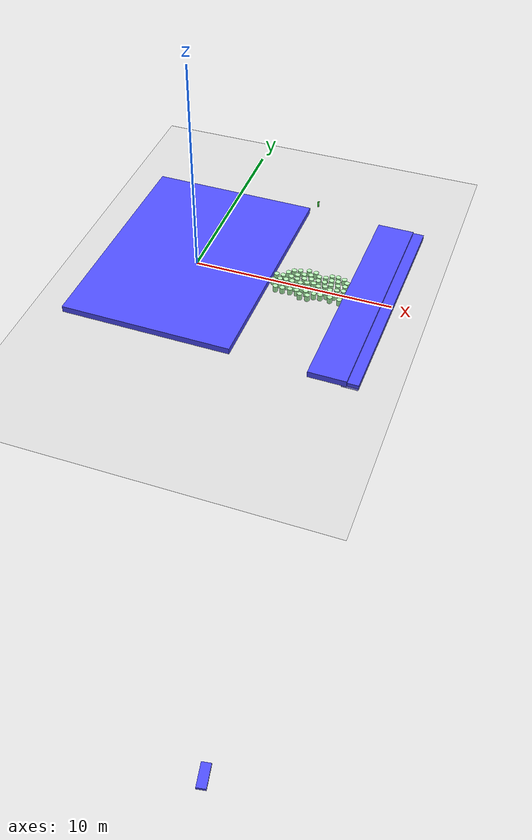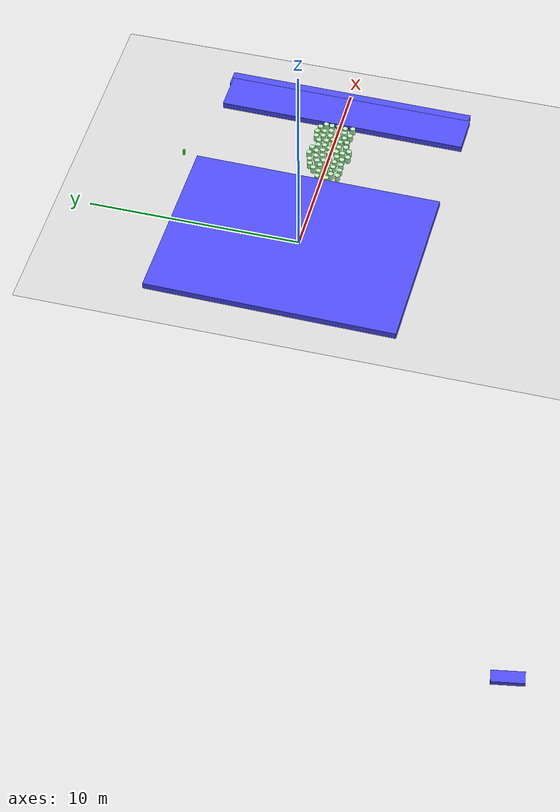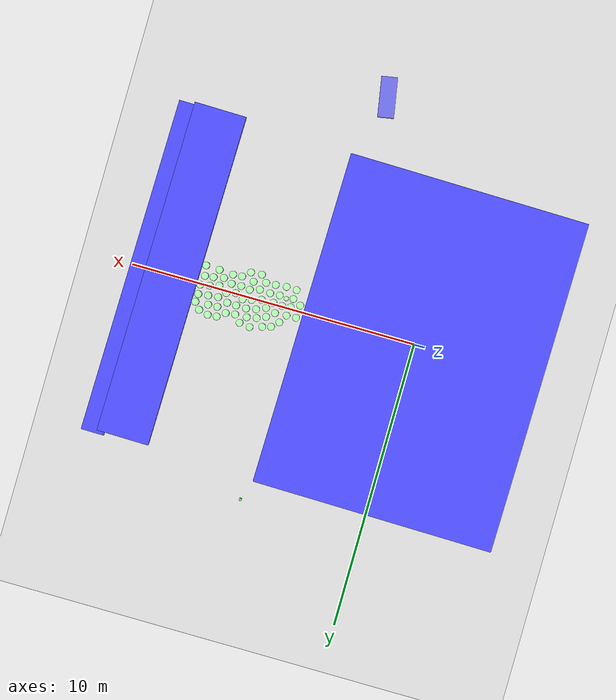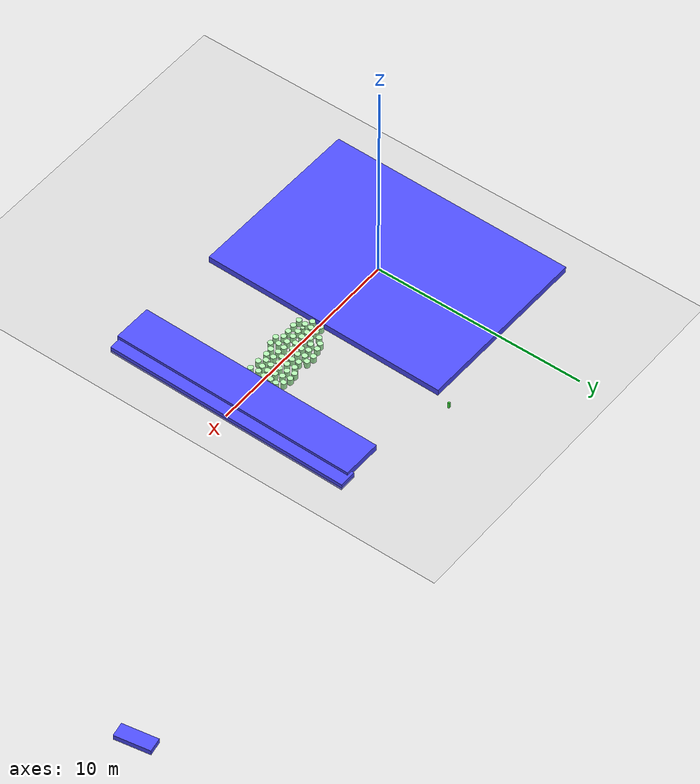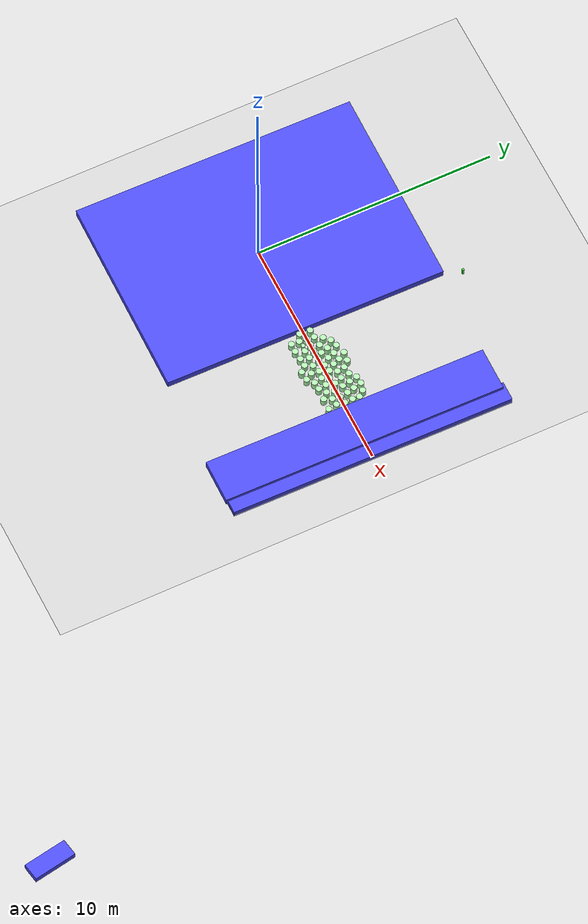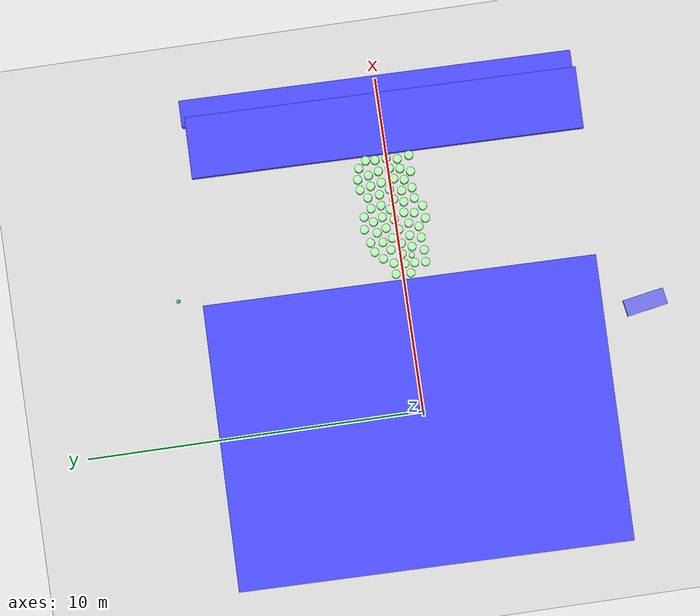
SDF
<sdf version="1.7">
 <world name="default">
  <light name="sun" type="directional">
   <pose>0 0 10 0 -0 0</pose>
   <diffuse>0.8 0.8 0.8 1</diffuse>
   <specular>0.2 0.2 0.2 1</specular>
   <attenuation>
    <range>1000</range>
    <constant>0.9</constant>
    <linear>0.01</linear>
    <quadratic>0.001</quadratic>
   </attenuation>
   <direction>-0.5 0.1 -0.9</direction>
   <spot><inner_angle>0</inner_angle><outer_angle>0</outer_angle><falloff>0</falloff></spot>
  </light>
  <model name="ground_plane">
   <static>1</static>
   <link name="link">
    <collision name="collision">
     <geometry><plane><normal>0 0 1</normal><size>100 100</size></plane></geometry>
     <surface><friction><ode><mu>100</mu><mu2>50</mu2></ode></friction></surface>
    </collision>
    <visual name="visual">
     <cast_shadows>0</cast_shadows>
     <geometry><plane><normal>0 0 1</normal><size>100 100</size></plane></geometry>
     <material>
      <script><uri>file://media/materials/scripts/gazebo.material</uri><name>Gazebo/Grey</name></script>
     </material>
    </visual>
   </link>
  </model>
  <gravity>0 0 -9.8</gravity>
  <magnetic_field>6e-06 2.3e-05 -4.2e-05</magnetic_field>
  <atmosphere type="adiabatic"/>
  <physics type="ode">
   <max_step_size>0.001</max_step_size>
   <real_time_factor>1</real_time_factor>
   <real_time_update_rate>1000</real_time_update_rate>
  </physics>
  <scene><ambient>0.4 0.4 0.4 1</ambient><background>0.7 0.7 0.7 1</background><shadows>1</shadows></scene>
  <spherical_coordinates>
   <surface_model>EARTH_WGS84</surface_model>
   <latitude_deg>0</latitude_deg>
   <longitude_deg>0</longitude_deg>
   <elevation>0</elevation>
   <heading_deg>0</heading_deg>
  </spherical_coordinates>
  <model name="ban_200_80_30_clone_clone">
   <link name="link">
    <inertial>
     <mass>1</mass>
     <inertia>
      <ixx>0.166667</ixx>
      <ixy>0</ixy>
      <ixz>0</ixz>
      <iyy>0.166667</iyy>
      <iyz>0</iyz>
      <izz>0.166667</izz>
     </inertia>
    </inertial>
    <visual name="visual">
     <geometry><box><size>2 0.8 0.3</size></box></geometry>
     <material>
      <script><name>Gazebo/Grey</name><uri>file://media/materials/scripts/gazebo.material</uri></script>
      <shader type="pixel"><normal_map>__default__</normal_map></shader>
      <ambient>0.3 0.3 1 1</ambient>
      <diffuse>0.7 0.7 0.7 1</diffuse>
      <specular>0.01 0.01 0.01 1</specular>
      <emissive>0 0 0 1</emissive>
     </material>
    </visual>
    <collision name="collision">
     <geometry><box><size>2 0.8 0.3</size></box></geometry>
     <surface>
      <friction>
       <ode><mu>1</mu><mu2>1</mu2><fdir1>0 0 0</fdir1><slip1>0</slip1><slip2>0</slip2></ode>
       <torsional>
        <coefficient>1</coefficient>
        <patch_radius>0</patch_radius>
        <surface_radius>0</surface_radius>
        <use_patch_radius>1</use_patch_radius>
        <ode><slip>0</slip></ode>
       </torsional>
      </friction>
      <bounce><restitution_coefficient>0</restitution_coefficient><threshold>1e+06</threshold></bounce>
      <contact>
       <collide_without_contact>0</collide_without_contact>
       <collide_without_contact_bitmask>1</collide_without_contact_bitmask>
       <collide_bitmask>1</collide_bitmask>
       <ode>
        <soft_cfm>0</soft_cfm>
        <soft_erp>0.2</soft_erp>
        <kp>1e+13</kp>
        <kd>1</kd>
        <max_vel>0.01</max_vel>
        <min_depth>0</min_depth>
       </ode>
       <bullet>
        <split_impulse>1</split_impulse>
        <split_impulse_penetration_threshold>-0.01</split_impulse_penetration_threshold>
        <soft_cfm>0</soft_cfm>
        <soft_erp>0.2</soft_erp>
        <kp>1e+13</kp>
        <kd>1</kd>
       </bullet>
      </contact>
     </surface>
    </collision>
   </link>
   <static>1</static>
   <pose>3.32802 -11.2985 -36.3188 0 0 -1.39548</pose>
  </model>
  <model name="ban_400_80_30_clone_clone">
   <link name="link">
    <inertial>
     <mass>1</mass>
     <inertia>
      <ixx>0.166667</ixx>
      <ixy>0</ixy>
      <ixz>0</ixz>
      <iyy>0.166667</iyy>
      <iyz>0</iyz>
      <izz>0.166667</izz>
     </inertia>
    </inertial>
    <visual name="visual">
     <geometry><box><size>11.703 8.48251 0.306303</size></box></geometry>
     <material>
      <script><name>Gazebo/Grey</name><uri>file://media/materials/scripts/gazebo.material</uri></script>
      <shader type="pixel"><normal_map>__default__</normal_map></shader>
      <ambient>0.3 0.3 1 1</ambient>
      <diffuse>0.7 0.7 0.7 1</diffuse>
      <specular>0.01 0.01 0.01 1</specular>
      <emissive>0 0 0 1</emissive>
     </material>
    </visual>
    <collision name="collision">
     <geometry><box><size>11.703 8.48251 0.306303</size></box></geometry>
     <surface>
      <friction>
       <ode><mu>1</mu><mu2>1</mu2><fdir1>0 0 0</fdir1><slip1>0</slip1><slip2>0</slip2></ode>
       <torsional>
        <coefficient>1</coefficient>
        <patch_radius>0</patch_radius>
        <surface_radius>0</surface_radius>
        <use_patch_radius>1</use_patch_radius>
        <ode><slip>0</slip></ode>
       </torsional>
      </friction>
      <bounce><restitution_coefficient>0</restitution_coefficient><threshold>1e+06</threshold></bounce>
      <contact>
       <collide_without_contact>0</collide_without_contact>
       <collide_without_contact_bitmask>1</collide_without_contact_bitmask>
       <collide_bitmask>1</collide_bitmask>
       <ode>
        <soft_cfm>0</soft_cfm>
        <soft_erp>0.2</soft_erp>
        <kp>1e+13</kp>
        <kd>1</kd>
        <max_vel>0.01</max_vel>
        <min_depth>0</min_depth>
       </ode>
       <bullet>
        <split_impulse>1</split_impulse>
        <split_impulse_penetration_threshold>-0.01</split_impulse_penetration_threshold>
        <soft_cfm>0</soft_cfm>
        <soft_erp>0.2</soft_erp>
        <kp>1e+13</kp>
        <kd>1</kd>
       </bullet>
      </contact>
     </surface>
    </collision>
   </link>
   <static>1</static>
   <pose>-0.303945 0.196417 0.141155 0 -0 1.55763</pose>
  </model>
  <model name="ban_400_80_30_clone">
   <link name="link">
    <inertial>
     <mass>1</mass>
     <inertia>
      <ixx>0.166667</ixx>
      <ixy>0</ixy>
      <ixz>0</ixz>
      <iyy>0.166667</iyy>
      <iyz>0</iyz>
      <izz>0.166667</izz>
     </inertia>
    </inertial>
    <visual name="visual">
     <geometry><box><size>11.7457 0.8 0.3</size></box></geometry>
     <material>
      <script><name>Gazebo/Grey</name><uri>file://media/materials/scripts/gazebo.material</uri></script>
      <shader type="pixel"><normal_map>__default__</normal_map></shader>
      <ambient>0.3 0.3 1 1</ambient>
      <diffuse>0.7 0.7 0.7 1</diffuse>
      <specular>0.01 0.01 0.01 1</specular>
      <emissive>0 0 0 1</emissive>
     </material>
    </visual>
    <collision name="collision">
     <geometry><box><size>11.7457 0.8 0.3</size></box></geometry>
     <surface>
      <friction>
       <ode><mu>1</mu><mu2>1</mu2><fdir1>0 0 0</fdir1><slip1>0</slip1><slip2>0</slip2></ode>
       <torsional>
        <coefficient>1</coefficient>
        <patch_radius>0</patch_radius>
        <surface_radius>0</surface_radius>
        <use_patch_radius>1</use_patch_radius>
        <ode><slip>0</slip></ode>
       </torsional>
      </friction>
      <bounce><restitution_coefficient>0</restitution_coefficient><threshold>1e+06</threshold></bounce>
      <contact>
       <collide_without_contact>0</collide_without_contact>
       <collide_without_contact_bitmask>1</collide_without_contact_bitmask>
       <collide_bitmask>1</collide_bitmask>
       <ode>
        <soft_cfm>0</soft_cfm>
        <soft_erp>0.2</soft_erp>
        <kp>1e+13</kp>
        <kd>1</kd>
        <max_vel>0.01</max_vel>
        <min_depth>0</min_depth>
       </ode>
       <bullet>
        <split_impulse>1</split_impulse>
        <split_impulse_penetration_threshold>-0.01</split_impulse_penetration_threshold>
        <soft_cfm>0</soft_cfm>
        <soft_erp>0.2</soft_erp>
        <kp>1e+13</kp>
        <kd>1</kd>
       </bullet>
      </contact>
     </surface>
    </collision>
   </link>
   <static>1</static>
   <pose>9.68721 0.016567 0 0 -0 1.55763</pose>
  </model>
  <model name="mhz_8_30_clone">
   <link name="link">
    <inertial>
     <mass>1</mass>
     <inertia>
      <ixx>0.166667</ixx>
      <ixy>0</ixy>
      <ixz>0</ixz>
      <iyy>0.166667</iyy>
      <iyz>0</iyz>
      <izz>0.166667</izz>
     </inertia>
    </inertial>
    <visual name="visual">
     <geometry><box><size>0.08 0.08 0.3</size></box></geometry>
     <material>
      <script><name>Gazebo/Grey</name><uri>file://media/materials/scripts/gazebo.material</uri></script>
      <shader type="pixel"><normal_map>__default__</normal_map></shader>
      <ambient>0.3 1 0.3 1</ambient>
      <diffuse>0.7 0.7 0.7 1</diffuse>
      <specular>0.01 0.01 0.01 1</specular>
      <emissive>0 0 0 1</emissive>
     </material>
    </visual>
    <collision name="collision">
     <geometry><box><size>0.08 0.08 0.3</size></box></geometry>
     <surface>
      <friction>
       <ode><mu>1</mu><mu2>1</mu2><fdir1>0 0 0</fdir1><slip1>0</slip1><slip2>0</slip2></ode>
       <torsional>
        <coefficient>1</coefficient>
        <patch_radius>0</patch_radius>
        <surface_radius>0</surface_radius>
        <use_patch_radius>1</use_patch_radius>
        <ode><slip>0</slip></ode>
       </torsional>
      </friction>
      <bounce><restitution_coefficient>0</restitution_coefficient><threshold>1e+06</threshold></bounce>
      <contact>
       <collide_without_contact>0</collide_without_contact>
       <collide_without_contact_bitmask>1</collide_without_contact_bitmask>
       <collide_bitmask>1</collide_bitmask>
       <ode>
        <soft_cfm>0</soft_cfm>
        <soft_erp>0.2</soft_erp>
        <kp>1e+13</kp>
        <kd>1</kd>
        <max_vel>0.01</max_vel>
        <min_depth>0</min_depth>
       </ode>
       <bullet>
        <split_impulse>1</split_impulse>
        <split_impulse_penetration_threshold>-0.01</split_impulse_penetration_threshold>
        <soft_cfm>0</soft_cfm>
        <soft_erp>0.2</soft_erp>
        <kp>1e+13</kp>
        <kd>1</kd>
       </bullet>
      </contact>
     </surface>
    </collision>
   </link>
   <static>1</static>
   <pose>4.25594 6.71166 0.134436 0 -0 0</pose>
  </model>
  <model name="mhz_y_25_30_clone">
   <link name="link">
    <inertial>
     <mass>1</mass>
     <inertia><ixx>0.145833</ixx><ixy>0</ixy><ixz>0</ixz><iyy>0.145833</iyy><iyz>0</iyz><izz>0.125</izz></inertia>
    </inertial>
    <visual name="visual">
     <geometry><cylinder><radius>0.125</radius><length>0.3</length></cylinder></geometry>
     <material>
      <script><name>Gazebo/Grey</name><uri>file://media/materials/scripts/gazebo.material</uri></script>
      <shader type="pixel"><normal_map>__default__</normal_map></shader>
      <ambient>0 1 0 0</ambient>
      <diffuse>0.7 1 0.7 1</diffuse>
      <specular>0.01 0.01 0.01 1</specular>
      <emissive>0 0 0 1</emissive>
     </material>
    </visual>
    <collision name="collision">
     <geometry><cylinder><radius>0.125</radius><length>0.3</length></cylinder></geometry>
     <surface>
      <friction>
       <ode><mu>1</mu><mu2>1</mu2><fdir1>0 0 0</fdir1><slip1>0</slip1><slip2>0</slip2></ode>
       <torsional>
        <coefficient>1</coefficient>
        <patch_radius>0</patch_radius>
        <surface_radius>0</surface_radius>
        <use_patch_radius>1</use_patch_radius>
        <ode><slip>0</slip></ode>
       </torsional>
      </friction>
      <bounce><restitution_coefficient>0</restitution_coefficient><threshold>1e+06</threshold></bounce>
      <contact>
       <collide_without_contact>0</collide_without_contact>
       <collide_without_contact_bitmask>1</collide_without_contact_bitmask>
       <collide_bitmask>1</collide_bitmask>
       <ode>
        <soft_cfm>0</soft_cfm>
        <soft_erp>0.2</soft_erp>
        <kp>1e+13</kp>
        <kd>1</kd>
        <max_vel>0.01</max_vel>
        <min_depth>0</min_depth>
       </ode>
       <bullet>
        <split_impulse>1</split_impulse>
        <split_impulse_penetration_threshold>-0.01</split_impulse_penetration_threshold>
        <soft_cfm>0</soft_cfm>
        <soft_erp>0.2</soft_erp>
        <kp>1e+13</kp>
        <kd>1</kd>
       </bullet>
      </contact>
     </surface>
    </collision>
   </link>
   <static>1</static>
   <pose>4.40569 -0.082911 0.14679 0 -0 0</pose>
  </model>
  <model name="mhz_y_25_30_clone_13">
   <link name="link">
    <inertial>
     <mass>1</mass>
     <inertia><ixx>0.145833</ixx><ixy>0</ixy><ixz>0</ixz><iyy>0.145833</iyy><iyz>0</iyz><izz>0.125</izz></inertia>
    </inertial>
    <visual name="visual">
     <geometry><cylinder><radius>0.125</radius><length>0.3</length></cylinder></geometry>
     <material>
      <script><name>Gazebo/Grey</name><uri>file://media/materials/scripts/gazebo.material</uri></script>
      <shader type="pixel"><normal_map>__default__</normal_map></shader>
      <ambient>0 1 0 0</ambient>
      <diffuse>0.7 1 0.7 1</diffuse>
      <specular>0.01 0.01 0.01 1</specular>
      <emissive>0 0 0 1</emissive>
     </material>
    </visual>
    <collision name="collision">
     <geometry><cylinder><radius>0.125</radius><length>0.3</length></cylinder></geometry>
     <surface>
      <friction>
       <ode><mu>1</mu><mu2>1</mu2><fdir1>0 0 0</fdir1><slip1>0</slip1><slip2>0</slip2></ode>
       <torsional>
        <coefficient>1</coefficient>
        <patch_radius>0</patch_radius>
        <surface_radius>0</surface_radius>
        <use_patch_radius>1</use_patch_radius>
        <ode><slip>0</slip></ode>
       </torsional>
      </friction>
      <bounce><restitution_coefficient>0</restitution_coefficient><threshold>1e+06</threshold></bounce>
      <contact>
       <collide_without_contact>0</collide_without_contact>
       <collide_without_contact_bitmask>1</collide_without_contact_bitmask>
       <collide_bitmask>1</collide_bitmask>
       <ode>
        <soft_cfm>0</soft_cfm>
        <soft_erp>0.2</soft_erp>
        <kp>1e+13</kp>
        <kd>1</kd>
        <max_vel>0.01</max_vel>
        <min_depth>0</min_depth>
       </ode>
       <bullet>
        <split_impulse>1</split_impulse>
        <split_impulse_penetration_threshold>-0.01</split_impulse_penetration_threshold>
        <soft_cfm>0</soft_cfm>
        <soft_erp>0.2</soft_erp>
        <kp>1e+13</kp>
        <kd>1</kd>
       </bullet>
      </contact>
     </surface>
    </collision>
   </link>
   <static>1</static>
   <pose>4.39388 -0.378997 0.14679 0 -0 0</pose>
  </model>
  <model name="ban_400_80_30_clone_clone_clone">
   <link name="link">
    <inertial>
     <mass>1</mass>
     <inertia>
      <ixx>0.166667</ixx>
      <ixy>0</ixy>
      <ixz>0</ixz>
      <iyy>0.166667</iyy>
      <iyz>0</iyz>
      <izz>0.166667</izz>
     </inertia>
    </inertial>
    <visual name="visual">
     <geometry><box><size>11.703 1.83242 0.3</size></box></geometry>
     <material>
      <script><name>Gazebo/Grey</name><uri>file://media/materials/scripts/gazebo.material</uri></script>
      <shader type="pixel"><normal_map>__default__</normal_map></shader>
      <ambient>0.3 0.3 1 1</ambient>
      <diffuse>0.7 0.7 0.7 1</diffuse>
      <specular>0.01 0.01 0.01 1</specular>
      <emissive>0 0 0 1</emissive>
     </material>
    </visual>
    <collision name="collision">
     <geometry><box><size>11.703 1.83242 0.3</size></box></geometry>
     <surface>
      <friction>
       <ode><mu>1</mu><mu2>1</mu2><fdir1>0 0 0</fdir1><slip1>0</slip1><slip2>0</slip2></ode>
       <torsional>
        <coefficient>1</coefficient>
        <patch_radius>0</patch_radius>
        <surface_radius>0</surface_radius>
        <use_patch_radius>1</use_patch_radius>
        <ode><slip>0</slip></ode>
       </torsional>
      </friction>
      <bounce><restitution_coefficient>0</restitution_coefficient><threshold>1e+06</threshold></bounce>
      <contact>
       <collide_without_contact>0</collide_without_contact>
       <collide_without_contact_bitmask>1</collide_without_contact_bitmask>
       <collide_bitmask>1</collide_bitmask>
       <ode>
        <soft_cfm>0</soft_cfm>
        <soft_erp>0.2</soft_erp>
        <kp>1e+13</kp>
        <kd>1</kd>
        <max_vel>0.01</max_vel>
        <min_depth>0</min_depth>
       </ode>
       <bullet>
        <split_impulse>1</split_impulse>
        <split_impulse_penetration_threshold>-0.01</split_impulse_penetration_threshold>
        <soft_cfm>0</soft_cfm>
        <soft_erp>0.2</soft_erp>
        <kp>1e+13</kp>
        <kd>1</kd>
       </bullet>
      </contact>
     </surface>
    </collision>
   </link>
   <static>1</static>
   <pose>8.63322 -0.071167 0.139007 0 -0 1.55763</pose>
  </model>
  <model name="mhz_y_25_30_clone_13_clone">
   <link name="link">
    <inertial>
     <mass>1</mass>
     <inertia><ixx>0.145833</ixx><ixy>0</ixy><ixz>0</ixz><iyy>0.145833</iyy><iyz>0</iyz><izz>0.125</izz></inertia>
    </inertial>
    <visual name="visual">
     <geometry><cylinder><radius>0.125</radius><length>0.3</length></cylinder></geometry>
     <material>
      <script><name>Gazebo/Grey</name><uri>file://media/materials/scripts/gazebo.material</uri></script>
      <shader type="pixel"><normal_map>__default__</normal_map></shader>
      <ambient>0 1 0 0</ambient>
      <diffuse>0.7 1 0.7 1</diffuse>
      <specular>0.01 0.01 0.01 1</specular>
      <emissive>0 0 0 1</emissive>
     </material>
    </visual>
    <collision name="collision">
     <geometry><cylinder><radius>0.125</radius><length>0.3</length></cylinder></geometry>
     <surface>
      <friction>
       <ode><mu>1</mu><mu2>1</mu2><fdir1>0 0 0</fdir1><slip1>0</slip1><slip2>0</slip2></ode>
       <torsional>
        <coefficient>1</coefficient>
        <patch_radius>0</patch_radius>
        <surface_radius>0</surface_radius>
        <use_patch_radius>1</use_patch_radius>
        <ode><slip>0</slip></ode>
       </torsional>
      </friction>
      <bounce><restitution_coefficient>0</restitution_coefficient><threshold>1e+06</threshold></bounce>
      <contact>
       <collide_without_contact>0</collide_without_contact>
       <collide_without_contact_bitmask>1</collide_without_contact_bitmask>
       <collide_bitmask>1</collide_bitmask>
       <ode>
        <soft_cfm>0</soft_cfm>
        <soft_erp>0.2</soft_erp>
        <kp>1e+13</kp>
        <kd>1</kd>
        <max_vel>0.01</max_vel>
        <min_depth>0</min_depth>
       </ode>
       <bullet>
        <split_impulse>1</split_impulse>
        <split_impulse_penetration_threshold>-0.01</split_impulse_penetration_threshold>
        <soft_cfm>0</soft_cfm>
        <soft_erp>0.2</soft_erp>
        <kp>1e+13</kp>
        <kd>1</kd>
       </bullet>
      </contact>
     </surface>
    </collision>
   </link>
   <static>1</static>
   <pose>4.46457 0.231285 0.14679 0 -0 0</pose>
  </model>
  <model name="mhz_y_25_30_clone_13_clone_0">
   <link name="link">
    <inertial>
     <mass>1</mass>
     <inertia><ixx>0.145833</ixx><ixy>0</ixy><ixz>0</ixz><iyy>0.145833</iyy><iyz>0</iyz><izz>0.125</izz></inertia>
    </inertial>
    <visual name="visual">
     <geometry><cylinder><radius>0.125</radius><length>0.3</length></cylinder></geometry>
     <material>
      <script><name>Gazebo/Grey</name><uri>file://media/materials/scripts/gazebo.material</uri></script>
      <shader type="pixel"><normal_map>__default__</normal_map></shader>
      <ambient>0 1 0 0</ambient>
      <diffuse>0.7 1 0.7 1</diffuse>
      <specular>0.01 0.01 0.01 1</specular>
      <emissive>0 0 0 1</emissive>
     </material>
    </visual>
    <collision name="collision">
     <geometry><cylinder><radius>0.125</radius><length>0.3</length></cylinder></geometry>
     <surface>
      <friction>
       <ode><mu>1</mu><mu2>1</mu2><fdir1>0 0 0</fdir1><slip1>0</slip1><slip2>0</slip2></ode>
       <torsional>
        <coefficient>1</coefficient>
        <patch_radius>0</patch_radius>
        <surface_radius>0</surface_radius>
        <use_patch_radius>1</use_patch_radius>
        <ode><slip>0</slip></ode>
       </torsional>
      </friction>
      <bounce><restitution_coefficient>0</restitution_coefficient><threshold>1e+06</threshold></bounce>
      <contact>
       <collide_without_contact>0</collide_without_contact>
       <collide_without_contact_bitmask>1</collide_without_contact_bitmask>
       <collide_bitmask>1</collide_bitmask>
       <ode>
        <soft_cfm>0</soft_cfm>
        <soft_erp>0.2</soft_erp>
        <kp>1e+13</kp>
        <kd>1</kd>
        <max_vel>0.01</max_vel>
        <min_depth>0</min_depth>
       </ode>
       <bullet>
        <split_impulse>1</split_impulse>
        <split_impulse_penetration_threshold>-0.01</split_impulse_penetration_threshold>
        <soft_cfm>0</soft_cfm>
        <soft_erp>0.2</soft_erp>
        <kp>1e+13</kp>
        <kd>1</kd>
       </bullet>
      </contact>
     </surface>
    </collision>
   </link>
   <static>1</static>
   <pose>4.70067 -0.046369 0.14679 0 -0 0</pose>
  </model>
  <model name="mhz_y_25_30_clone_13_clone_1">
   <link name="link">
    <inertial>
     <mass>1</mass>
     <inertia><ixx>0.145833</ixx><ixy>0</ixy><ixz>0</ixz><iyy>0.145833</iyy><iyz>0</iyz><izz>0.125</izz></inertia>
    </inertial>
    <visual name="visual">
     <geometry><cylinder><radius>0.125</radius><length>0.3</length></cylinder></geometry>
     <material>
      <script><name>Gazebo/Grey</name><uri>file://media/materials/scripts/gazebo.material</uri></script>
      <shader type="pixel"><normal_map>__default__</normal_map></shader>
      <ambient>0 1 0 0</ambient>
      <diffuse>0.7 1 0.7 1</diffuse>
      <specular>0.01 0.01 0.01 1</specular>
      <emissive>0 0 0 1</emissive>
     </material>
    </visual>
    <collision name="collision">
     <geometry><cylinder><radius>0.125</radius><length>0.3</length></cylinder></geometry>
     <surface>
      <friction>
       <ode><mu>1</mu><mu2>1</mu2><fdir1>0 0 0</fdir1><slip1>0</slip1><slip2>0</slip2></ode>
       <torsional>
        <coefficient>1</coefficient>
        <patch_radius>0</patch_radius>
        <surface_radius>0</surface_radius>
        <use_patch_radius>1</use_patch_radius>
        <ode><slip>0</slip></ode>
       </torsional>
      </friction>
      <bounce><restitution_coefficient>0</restitution_coefficient><threshold>1e+06</threshold></bounce>
      <contact>
       <collide_without_contact>0</collide_without_contact>
       <collide_without_contact_bitmask>1</collide_without_contact_bitmask>
       <collide_bitmask>1</collide_bitmask>
       <ode>
        <soft_cfm>0</soft_cfm>
        <soft_erp>0.2</soft_erp>
        <kp>1e+13</kp>
        <kd>1</kd>
        <max_vel>0.01</max_vel>
        <min_depth>0</min_depth>
       </ode>
       <bullet>
        <split_impulse>1</split_impulse>
        <split_impulse_penetration_threshold>-0.01</split_impulse_penetration_threshold>
        <soft_cfm>0</soft_cfm>
        <soft_erp>0.2</soft_erp>
        <kp>1e+13</kp>
        <kd>1</kd>
       </bullet>
      </contact>
     </surface>
    </collision>
   </link>
   <static>1</static>
   <pose>4.87552 -0.370789 0.14679 0 -0 0</pose>
  </model>
  <model name="mhz_y_25_30_clone_13_clone_2">
   <link name="link">
    <inertial>
     <mass>1</mass>
     <inertia><ixx>0.145833</ixx><ixy>0</ixy><ixz>0</ixz><iyy>0.145833</iyy><iyz>0</iyz><izz>0.125</izz></inertia>
    </inertial>
    <visual name="visual">
     <geometry><cylinder><radius>0.125</radius><length>0.3</length></cylinder></geometry>
     <material>
      <script><name>Gazebo/Grey</name><uri>file://media/materials/scripts/gazebo.material</uri></script>
      <shader type="pixel"><normal_map>__default__</normal_map></shader>
      <ambient>0 1 0 0</ambient>
      <diffuse>0.7 1 0.7 1</diffuse>
      <specular>0.01 0.01 0.01 1</specular>
      <emissive>0 0 0 1</emissive>
     </material>
    </visual>
    <collision name="collision">
     <geometry><cylinder><radius>0.125</radius><length>0.3</length></cylinder></geometry>
     <surface>
      <friction>
       <ode><mu>1</mu><mu2>1</mu2><fdir1>0 0 0</fdir1><slip1>0</slip1><slip2>0</slip2></ode>
       <torsional>
        <coefficient>1</coefficient>
        <patch_radius>0</patch_radius>
        <surface_radius>0</surface_radius>
        <use_patch_radius>1</use_patch_radius>
        <ode><slip>0</slip></ode>
       </torsional>
      </friction>
      <bounce><restitution_coefficient>0</restitution_coefficient><threshold>1e+06</threshold></bounce>
      <contact>
       <collide_without_contact>0</collide_without_contact>
       <collide_without_contact_bitmask>1</collide_without_contact_bitmask>
       <collide_bitmask>1</collide_bitmask>
       <ode>
        <soft_cfm>0</soft_cfm>
        <soft_erp>0.2</soft_erp>
        <kp>1e+13</kp>
        <kd>1</kd>
        <max_vel>0.01</max_vel>
        <min_depth>0</min_depth>
       </ode>
       <bullet>
        <split_impulse>1</split_impulse>
        <split_impulse_penetration_threshold>-0.01</split_impulse_penetration_threshold>
        <soft_cfm>0</soft_cfm>
        <soft_erp>0.2</soft_erp>
        <kp>1e+13</kp>
        <kd>1</kd>
       </bullet>
      </contact>
     </surface>
    </collision>
   </link>
   <static>1</static>
   <pose>4.72883 -0.713861 0.14679 0 -0 0</pose>
  </model>
  <model name="mhz_y_25_30_clone_13_clone_3">
   <link name="link">
    <inertial>
     <mass>1</mass>
     <inertia><ixx>0.145833</ixx><ixy>0</ixy><ixz>0</ixz><iyy>0.145833</iyy><iyz>0</iyz><izz>0.125</izz></inertia>
    </inertial>
    <visual name="visual">
     <geometry><cylinder><radius>0.125</radius><length>0.3</length></cylinder></geometry>
     <material>
      <script><name>Gazebo/Grey</name><uri>file://media/materials/scripts/gazebo.material</uri></script>
      <shader type="pixel"><normal_map>__default__</normal_map></shader>
      <ambient>0 1 0 0</ambient>
      <diffuse>0.7 1 0.7 1</diffuse>
      <specular>0.01 0.01 0.01 1</specular>
      <emissive>0 0 0 1</emissive>
     </material>
    </visual>
    <collision name="collision">
     <geometry><cylinder><radius>0.125</radius><length>0.3</length></cylinder></geometry>
     <surface>
      <friction>
       <ode><mu>1</mu><mu2>1</mu2><fdir1>0 0 0</fdir1><slip1>0</slip1><slip2>0</slip2></ode>
       <torsional>
        <coefficient>1</coefficient>
        <patch_radius>0</patch_radius>
        <surface_radius>0</surface_radius>
        <use_patch_radius>1</use_patch_radius>
        <ode><slip>0</slip></ode>
       </torsional>
      </friction>
      <bounce><restitution_coefficient>0</restitution_coefficient><threshold>1e+06</threshold></bounce>
      <contact>
       <collide_without_contact>0</collide_without_contact>
       <collide_without_contact_bitmask>1</collide_without_contact_bitmask>
       <collide_bitmask>1</collide_bitmask>
       <ode>
        <soft_cfm>0</soft_cfm>
        <soft_erp>0.2</soft_erp>
        <kp>1e+13</kp>
        <kd>1</kd>
        <max_vel>0.01</max_vel>
        <min_depth>0</min_depth>
       </ode>
       <bullet>
        <split_impulse>1</split_impulse>
        <split_impulse_penetration_threshold>-0.01</split_impulse_penetration_threshold>
        <soft_cfm>0</soft_cfm>
        <soft_erp>0.2</soft_erp>
        <kp>1e+13</kp>
        <kd>1</kd>
       </bullet>
      </contact>
     </surface>
    </collision>
   </link>
   <static>1</static>
   <pose>5.01371 -0.066974 0.14679 0 -0 0</pose>
  </model>
  <model name="mhz_y_25_30_clone_13_clone_4">
   <link name="link">
    <inertial>
     <mass>1</mass>
     <inertia><ixx>0.145833</ixx><ixy>0</ixy><ixz>0</ixz><iyy>0.145833</iyy><iyz>0</iyz><izz>0.125</izz></inertia>
    </inertial>
    <visual name="visual">
     <geometry><cylinder><radius>0.125</radius><length>0.3</length></cylinder></geometry>
     <material>
      <script><name>Gazebo/Grey</name><uri>file://media/materials/scripts/gazebo.material</uri></script>
      <shader type="pixel"><normal_map>__default__</normal_map></shader>
      <ambient>0 1 0 0</ambient>
      <diffuse>0.7 1 0.7 1</diffuse>
      <specular>0.01 0.01 0.01 1</specular>
      <emissive>0 0 0 1</emissive>
     </material>
    </visual>
    <collision name="collision">
     <geometry><cylinder><radius>0.125</radius><length>0.3</length></cylinder></geometry>
     <surface>
      <friction>
       <ode><mu>1</mu><mu2>1</mu2><fdir1>0 0 0</fdir1><slip1>0</slip1><slip2>0</slip2></ode>
       <torsional>
        <coefficient>1</coefficient>
        <patch_radius>0</patch_radius>
        <surface_radius>0</surface_radius>
        <use_patch_radius>1</use_patch_radius>
        <ode><slip>0</slip></ode>
       </torsional>
      </friction>
      <bounce><restitution_coefficient>0</restitution_coefficient><threshold>1e+06</threshold></bounce>
      <contact>
       <collide_without_contact>0</collide_without_contact>
       <collide_without_contact_bitmask>1</collide_without_contact_bitmask>
       <collide_bitmask>1</collide_bitmask>
       <ode>
        <soft_cfm>0</soft_cfm>
        <soft_erp>0.2</soft_erp>
        <kp>1e+13</kp>
        <kd>1</kd>
        <max_vel>0.01</max_vel>
        <min_depth>0</min_depth>
       </ode>
       <bullet>
        <split_impulse>1</split_impulse>
        <split_impulse_penetration_threshold>-0.01</split_impulse_penetration_threshold>
        <soft_cfm>0</soft_cfm>
        <soft_erp>0.2</soft_erp>
        <kp>1e+13</kp>
        <kd>1</kd>
       </bullet>
      </contact>
     </surface>
    </collision>
   </link>
   <static>1</static>
   <pose>4.8668 0.259687 0.14679 0 -0 0</pose>
  </model>
  <model name="mhz_y_25_30_clone_13_clone_5">
   <link name="link">
    <inertial>
     <mass>1</mass>
     <inertia><ixx>0.145833</ixx><ixy>0</ixy><ixz>0</ixz><iyy>0.145833</iyy><iyz>0</iyz><izz>0.125</izz></inertia>
    </inertial>
    <visual name="visual">
     <geometry><cylinder><radius>0.125</radius><length>0.3</length></cylinder></geometry>
     <material>
      <script><name>Gazebo/Grey</name><uri>file://media/materials/scripts/gazebo.material</uri></script>
      <shader type="pixel"><normal_map>__default__</normal_map></shader>
      <ambient>0 1 0 0</ambient>
      <diffuse>0.7 1 0.7 1</diffuse>
      <specular>0.01 0.01 0.01 1</specular>
      <emissive>0 0 0 1</emissive>
     </material>
    </visual>
    <collision name="collision">
     <geometry><cylinder><radius>0.125</radius><length>0.3</length></cylinder></geometry>
     <surface>
      <friction>
       <ode><mu>1</mu><mu2>1</mu2><fdir1>0 0 0</fdir1><slip1>0</slip1><slip2>0</slip2></ode>
       <torsional>
        <coefficient>1</coefficient>
        <patch_radius>0</patch_radius>
        <surface_radius>0</surface_radius>
        <use_patch_radius>1</use_patch_radius>
        <ode><slip>0</slip></ode>
       </torsional>
      </friction>
      <bounce><restitution_coefficient>0</restitution_coefficient><threshold>1e+06</threshold></bounce>
      <contact>
       <collide_without_contact>0</collide_without_contact>
       <collide_without_contact_bitmask>1</collide_without_contact_bitmask>
       <collide_bitmask>1</collide_bitmask>
       <ode>
        <soft_cfm>0</soft_cfm>
        <soft_erp>0.2</soft_erp>
        <kp>1e+13</kp>
        <kd>1</kd>
        <max_vel>0.01</max_vel>
        <min_depth>0</min_depth>
       </ode>
       <bullet>
        <split_impulse>1</split_impulse>
        <split_impulse_penetration_threshold>-0.01</split_impulse_penetration_threshold>
        <soft_cfm>0</soft_cfm>
        <soft_erp>0.2</soft_erp>
        <kp>1e+13</kp>
        <kd>1</kd>
       </bullet>
      </contact>
     </surface>
    </collision>
   </link>
   <static>1</static>
   <pose>5.20718 0.170474 0.14679 0 -0 0</pose>
  </model>
  <model name="mhz_y_25_30_clone_13_clone_6">
   <link name="link">
    <inertial>
     <mass>1</mass>
     <inertia><ixx>0.145833</ixx><ixy>0</ixy><ixz>0</ixz><iyy>0.145833</iyy><iyz>0</iyz><izz>0.125</izz></inertia>
    </inertial>
    <visual name="visual">
     <geometry><cylinder><radius>0.125</radius><length>0.3</length></cylinder></geometry>
     <material>
      <script><name>Gazebo/Grey</name><uri>file://media/materials/scripts/gazebo.material</uri></script>
      <shader type="pixel"><normal_map>__default__</normal_map></shader>
      <ambient>0 1 0 0</ambient>
      <diffuse>0.7 1 0.7 1</diffuse>
      <specular>0.01 0.01 0.01 1</specular>
      <emissive>0 0 0 1</emissive>
     </material>
    </visual>
    <collision name="collision">
     <geometry><cylinder><radius>0.125</radius><length>0.3</length></cylinder></geometry>
     <surface>
      <friction>
       <ode><mu>1</mu><mu2>1</mu2><fdir1>0 0 0</fdir1><slip1>0</slip1><slip2>0</slip2></ode>
       <torsional>
        <coefficient>1</coefficient>
        <patch_radius>0</patch_radius>
        <surface_radius>0</surface_radius>
        <use_patch_radius>1</use_patch_radius>
        <ode><slip>0</slip></ode>
       </torsional>
      </friction>
      <bounce><restitution_coefficient>0</restitution_coefficient><threshold>1e+06</threshold></bounce>
      <contact>
       <collide_without_contact>0</collide_without_contact>
       <collide_without_contact_bitmask>1</collide_without_contact_bitmask>
       <collide_bitmask>1</collide_bitmask>
       <ode>
        <soft_cfm>0</soft_cfm>
        <soft_erp>0.2</soft_erp>
        <kp>1e+13</kp>
        <kd>1</kd>
        <max_vel>0.01</max_vel>
        <min_depth>0</min_depth>
       </ode>
       <bullet>
        <split_impulse>1</split_impulse>
        <split_impulse_penetration_threshold>-0.01</split_impulse_penetration_threshold>
        <soft_cfm>0</soft_cfm>
        <soft_erp>0.2</soft_erp>
        <kp>1e+13</kp>
        <kd>1</kd>
       </bullet>
      </contact>
     </surface>
    </collision>
   </link>
   <static>1</static>
   <pose>5.21197 -0.349892 0.14679 0 -0 0</pose>
  </model>
  <model name="mhz_y_25_30_clone_13_clone_7">
   <link name="link">
    <inertial>
     <mass>1</mass>
     <inertia><ixx>0.145833</ixx><ixy>0</ixy><ixz>0</ixz><iyy>0.145833</iyy><iyz>0</iyz><izz>0.125</izz></inertia>
    </inertial>
    <visual name="visual">
     <geometry><cylinder><radius>0.125</radius><length>0.3</length></cylinder></geometry>
     <material>
      <script><name>Gazebo/Grey</name><uri>file://media/materials/scripts/gazebo.material</uri></script>
      <shader type="pixel"><normal_map>__default__</normal_map></shader>
      <ambient>0 1 0 0</ambient>
      <diffuse>0.7 1 0.7 1</diffuse>
      <specular>0.01 0.01 0.01 1</specular>
      <emissive>0 0 0 1</emissive>
     </material>
    </visual>
    <collision name="collision">
     <geometry><cylinder><radius>0.125</radius><length>0.3</length></cylinder></geometry>
     <surface>
      <friction>
       <ode><mu>1</mu><mu2>1</mu2><fdir1>0 0 0</fdir1><slip1>0</slip1><slip2>0</slip2></ode>
       <torsional>
        <coefficient>1</coefficient>
        <patch_radius>0</patch_radius>
        <surface_radius>0</surface_radius>
        <use_patch_radius>1</use_patch_radius>
        <ode><slip>0</slip></ode>
       </torsional>
      </friction>
      <bounce><restitution_coefficient>0</restitution_coefficient><threshold>1e+06</threshold></bounce>
      <contact>
       <collide_without_contact>0</collide_without_contact>
       <collide_without_contact_bitmask>1</collide_without_contact_bitmask>
       <collide_bitmask>1</collide_bitmask>
       <ode>
        <soft_cfm>0</soft_cfm>
        <soft_erp>0.2</soft_erp>
        <kp>1e+13</kp>
        <kd>1</kd>
        <max_vel>0.01</max_vel>
        <min_depth>0</min_depth>
       </ode>
       <bullet>
        <split_impulse>1</split_impulse>
        <split_impulse_penetration_threshold>-0.01</split_impulse_penetration_threshold>
        <soft_cfm>0</soft_cfm>
        <soft_erp>0.2</soft_erp>
        <kp>1e+13</kp>
        <kd>1</kd>
       </bullet>
      </contact>
     </surface>
    </collision>
   </link>
   <static>1</static>
   <pose>5.10414 -0.678124 0.14679 0 -0 0</pose>
  </model>
  <model name="mhz_y_25_30_clone_13_clone_8">
   <link name="link">
    <inertial>
     <mass>1</mass>
     <inertia><ixx>0.145833</ixx><ixy>0</ixy><ixz>0</ixz><iyy>0.145833</iyy><iyz>0</iyz><izz>0.125</izz></inertia>
    </inertial>
    <visual name="visual">
     <geometry><cylinder><radius>0.125</radius><length>0.3</length></cylinder></geometry>
     <material>
      <script><name>Gazebo/Grey</name><uri>file://media/materials/scripts/gazebo.material</uri></script>
      <shader type="pixel"><normal_map>__default__</normal_map></shader>
      <ambient>0 1 0 0</ambient>
      <diffuse>0.7 1 0.7 1</diffuse>
      <specular>0.01 0.01 0.01 1</specular>
      <emissive>0 0 0 1</emissive>
     </material>
    </visual>
    <collision name="collision">
     <geometry><cylinder><radius>0.125</radius><length>0.3</length></cylinder></geometry>
     <surface>
      <friction>
       <ode><mu>1</mu><mu2>1</mu2><fdir1>0 0 0</fdir1><slip1>0</slip1><slip2>0</slip2></ode>
       <torsional>
        <coefficient>1</coefficient>
        <patch_radius>0</patch_radius>
        <surface_radius>0</surface_radius>
        <use_patch_radius>1</use_patch_radius>
        <ode><slip>0</slip></ode>
       </torsional>
      </friction>
      <bounce><restitution_coefficient>0</restitution_coefficient><threshold>1e+06</threshold></bounce>
      <contact>
       <collide_without_contact>0</collide_without_contact>
       <collide_without_contact_bitmask>1</collide_without_contact_bitmask>
       <collide_bitmask>1</collide_bitmask>
       <ode>
        <soft_cfm>0</soft_cfm>
        <soft_erp>0.2</soft_erp>
        <kp>1e+13</kp>
        <kd>1</kd>
        <max_vel>0.01</max_vel>
        <min_depth>0</min_depth>
       </ode>
       <bullet>
        <split_impulse>1</split_impulse>
        <split_impulse_penetration_threshold>-0.01</split_impulse_penetration_threshold>
        <soft_cfm>0</soft_cfm>
        <soft_erp>0.2</soft_erp>
        <kp>1e+13</kp>
        <kd>1</kd>
       </bullet>
      </contact>
     </surface>
    </collision>
   </link>
   <static>1</static>
   <pose>5.43473 -0.058627 0.14679 0 -0 0</pose>
  </model>
  <model name="mhz_y_25_30_clone_13_clone_9">
   <link name="link">
    <inertial>
     <mass>1</mass>
     <inertia><ixx>0.145833</ixx><ixy>0</ixy><ixz>0</ixz><iyy>0.145833</iyy><iyz>0</iyz><izz>0.125</izz></inertia>
    </inertial>
    <visual name="visual">
     <geometry><cylinder><radius>0.125</radius><length>0.3</length></cylinder></geometry>
     <material>
      <script><name>Gazebo/Grey</name><uri>file://media/materials/scripts/gazebo.material</uri></script>
      <shader type="pixel"><normal_map>__default__</normal_map></shader>
      <ambient>0 1 0 0</ambient>
      <diffuse>0.7 1 0.7 1</diffuse>
      <specular>0.01 0.01 0.01 1</specular>
      <emissive>0 0 0 1</emissive>
     </material>
    </visual>
    <collision name="collision">
     <geometry><cylinder><radius>0.125</radius><length>0.3</length></cylinder></geometry>
     <surface>
      <friction>
       <ode><mu>1</mu><mu2>1</mu2><fdir1>0 0 0</fdir1><slip1>0</slip1><slip2>0</slip2></ode>
       <torsional>
        <coefficient>1</coefficient>
        <patch_radius>0</patch_radius>
        <surface_radius>0</surface_radius>
        <use_patch_radius>1</use_patch_radius>
        <ode><slip>0</slip></ode>
       </torsional>
      </friction>
      <bounce><restitution_coefficient>0</restitution_coefficient><threshold>1e+06</threshold></bounce>
      <contact>
       <collide_without_contact>0</collide_without_contact>
       <collide_without_contact_bitmask>1</collide_without_contact_bitmask>
       <collide_bitmask>1</collide_bitmask>
       <ode>
        <soft_cfm>0</soft_cfm>
        <soft_erp>0.2</soft_erp>
        <kp>1e+13</kp>
        <kd>1</kd>
        <max_vel>0.01</max_vel>
        <min_depth>0</min_depth>
       </ode>
       <bullet>
        <split_impulse>1</split_impulse>
        <split_impulse_penetration_threshold>-0.01</split_impulse_penetration_threshold>
        <soft_cfm>0</soft_cfm>
        <soft_erp>0.2</soft_erp>
        <kp>1e+13</kp>
        <kd>1</kd>
       </bullet>
      </contact>
     </surface>
    </collision>
   </link>
   <static>1</static>
   <pose>5.12285 0.466035 0.14679 0 -0 0</pose>
  </model>
  <model name="mhz_y_25_30_clone_13_clone_10">
   <link name="link">
    <inertial>
     <mass>1</mass>
     <inertia><ixx>0.145833</ixx><ixy>0</ixy><ixz>0</ixz><iyy>0.145833</iyy><iyz>0</iyz><izz>0.125</izz></inertia>
    </inertial>
    <visual name="visual">
     <geometry><cylinder><radius>0.125</radius><length>0.3</length></cylinder></geometry>
     <material>
      <script><name>Gazebo/Grey</name><uri>file://media/materials/scripts/gazebo.material</uri></script>
      <shader type="pixel"><normal_map>__default__</normal_map></shader>
      <ambient>0 1 0 0</ambient>
      <diffuse>0.7 1 0.7 1</diffuse>
      <specular>0.01 0.01 0.01 1</specular>
      <emissive>0 0 0 1</emissive>
     </material>
    </visual>
    <collision name="collision">
     <geometry><cylinder><radius>0.125</radius><length>0.3</length></cylinder></geometry>
     <surface>
      <friction>
       <ode><mu>1</mu><mu2>1</mu2><fdir1>0 0 0</fdir1><slip1>0</slip1><slip2>0</slip2></ode>
       <torsional>
        <coefficient>1</coefficient>
        <patch_radius>0</patch_radius>
        <surface_radius>0</surface_radius>
        <use_patch_radius>1</use_patch_radius>
        <ode><slip>0</slip></ode>
       </torsional>
      </friction>
      <bounce><restitution_coefficient>0</restitution_coefficient><threshold>1e+06</threshold></bounce>
      <contact>
       <collide_without_contact>0</collide_without_contact>
       <collide_without_contact_bitmask>1</collide_without_contact_bitmask>
       <collide_bitmask>1</collide_bitmask>
       <ode>
        <soft_cfm>0</soft_cfm>
        <soft_erp>0.2</soft_erp>
        <kp>1e+13</kp>
        <kd>1</kd>
        <max_vel>0.01</max_vel>
        <min_depth>0</min_depth>
       </ode>
       <bullet>
        <split_impulse>1</split_impulse>
        <split_impulse_penetration_threshold>-0.01</split_impulse_penetration_threshold>
        <soft_cfm>0</soft_cfm>
        <soft_erp>0.2</soft_erp>
        <kp>1e+13</kp>
        <kd>1</kd>
       </bullet>
      </contact>
     </surface>
    </collision>
   </link>
   <static>1</static>
   <pose>4.63702 0.522884 0.14679 0 -0 0</pose>
  </model>
  <model name="mhz_y_25_30_clone_13_clone_11">
   <link name="link">
    <inertial>
     <mass>1</mass>
     <inertia><ixx>0.145833</ixx><ixy>0</ixy><ixz>0</ixz><iyy>0.145833</iyy><iyz>0</iyz><izz>0.125</izz></inertia>
    </inertial>
    <visual name="visual">
     <geometry><cylinder><radius>0.125</radius><length>0.3</length></cylinder></geometry>
     <material>
      <script><name>Gazebo/Grey</name><uri>file://media/materials/scripts/gazebo.material</uri></script>
      <shader type="pixel"><normal_map>__default__</normal_map></shader>
      <ambient>0 1 0 0</ambient>
      <diffuse>0.7 1 0.7 1</diffuse>
      <specular>0.01 0.01 0.01 1</specular>
      <emissive>0 0 0 1</emissive>
     </material>
    </visual>
    <collision name="collision">
     <geometry><cylinder><radius>0.125</radius><length>0.3</length></cylinder></geometry>
     <surface>
      <friction>
       <ode><mu>1</mu><mu2>1</mu2><fdir1>0 0 0</fdir1><slip1>0</slip1><slip2>0</slip2></ode>
       <torsional>
        <coefficient>1</coefficient>
        <patch_radius>0</patch_radius>
        <surface_radius>0</surface_radius>
        <use_patch_radius>1</use_patch_radius>
        <ode><slip>0</slip></ode>
       </torsional>
      </friction>
      <bounce><restitution_coefficient>0</restitution_coefficient><threshold>1e+06</threshold></bounce>
      <contact>
       <collide_without_contact>0</collide_without_contact>
       <collide_without_contact_bitmask>1</collide_without_contact_bitmask>
       <collide_bitmask>1</collide_bitmask>
       <ode>
        <soft_cfm>0</soft_cfm>
        <soft_erp>0.2</soft_erp>
        <kp>1e+13</kp>
        <kd>1</kd>
        <max_vel>0.01</max_vel>
        <min_depth>0</min_depth>
       </ode>
       <bullet>
        <split_impulse>1</split_impulse>
        <split_impulse_penetration_threshold>-0.01</split_impulse_penetration_threshold>
        <soft_cfm>0</soft_cfm>
        <soft_erp>0.2</soft_erp>
        <kp>1e+13</kp>
        <kd>1</kd>
       </bullet>
      </contact>
     </surface>
    </collision>
   </link>
   <static>1</static>
   <pose>5.52407 0.310951 0.14679 0 -0 0</pose>
  </model>
  <model name="mhz_y_25_30_clone_13_clone_12">
   <link name="link">
    <inertial>
     <mass>1</mass>
     <inertia><ixx>0.145833</ixx><ixy>0</ixy><ixz>0</ixz><iyy>0.145833</iyy><iyz>0</iyz><izz>0.125</izz></inertia>
    </inertial>
    <visual name="visual">
     <geometry><cylinder><radius>0.125</radius><length>0.3</length></cylinder></geometry>
     <material>
      <script><name>Gazebo/Grey</name><uri>file://media/materials/scripts/gazebo.material</uri></script>
      <shader type="pixel"><normal_map>__default__</normal_map></shader>
      <ambient>0 1 0 0</ambient>
      <diffuse>0.7 1 0.7 1</diffuse>
      <specular>0.01 0.01 0.01 1</specular>
      <emissive>0 0 0 1</emissive>
     </material>
    </visual>
    <collision name="collision">
     <geometry><cylinder><radius>0.125</radius><length>0.3</length></cylinder></geometry>
     <surface>
      <friction>
       <ode><mu>1</mu><mu2>1</mu2><fdir1>0 0 0</fdir1><slip1>0</slip1><slip2>0</slip2></ode>
       <torsional>
        <coefficient>1</coefficient>
        <patch_radius>0</patch_radius>
        <surface_radius>0</surface_radius>
        <use_patch_radius>1</use_patch_radius>
        <ode><slip>0</slip></ode>
       </torsional>
      </friction>
      <bounce><restitution_coefficient>0</restitution_coefficient><threshold>1e+06</threshold></bounce>
      <contact>
       <collide_without_contact>0</collide_without_contact>
       <collide_without_contact_bitmask>1</collide_without_contact_bitmask>
       <collide_bitmask>1</collide_bitmask>
       <ode>
        <soft_cfm>0</soft_cfm>
        <soft_erp>0.2</soft_erp>
        <kp>1e+13</kp>
        <kd>1</kd>
        <max_vel>0.01</max_vel>
        <min_depth>0</min_depth>
       </ode>
       <bullet>
        <split_impulse>1</split_impulse>
        <split_impulse_penetration_threshold>-0.01</split_impulse_penetration_threshold>
        <soft_cfm>0</soft_cfm>
        <soft_erp>0.2</soft_erp>
        <kp>1e+13</kp>
        <kd>1</kd>
       </bullet>
      </contact>
     </surface>
    </collision>
   </link>
   <static>1</static>
   <pose>5.85996 0.375597 0.14679 0 -0 0</pose>
  </model>
  <model name="mhz_y_25_30_clone_13_clone_13">
   <link name="link">
    <inertial>
     <mass>1</mass>
     <inertia><ixx>0.145833</ixx><ixy>0</ixy><ixz>0</ixz><iyy>0.145833</iyy><iyz>0</iyz><izz>0.125</izz></inertia>
    </inertial>
    <visual name="visual">
     <geometry><cylinder><radius>0.125</radius><length>0.3</length></cylinder></geometry>
     <material>
      <script><name>Gazebo/Grey</name><uri>file://media/materials/scripts/gazebo.material</uri></script>
      <shader type="pixel"><normal_map>__default__</normal_map></shader>
      <ambient>0 1 0 0</ambient>
      <diffuse>0.7 1 0.7 1</diffuse>
      <specular>0.01 0.01 0.01 1</specular>
      <emissive>0 0 0 1</emissive>
     </material>
    </visual>
    <collision name="collision">
     <geometry><cylinder><radius>0.125</radius><length>0.3</length></cylinder></geometry>
     <surface>
      <friction>
       <ode><mu>1</mu><mu2>1</mu2><fdir1>0 0 0</fdir1><slip1>0</slip1><slip2>0</slip2></ode>
       <torsional>
        <coefficient>1</coefficient>
        <patch_radius>0</patch_radius>
        <surface_radius>0</surface_radius>
        <use_patch_radius>1</use_patch_radius>
        <ode><slip>0</slip></ode>
       </torsional>
      </friction>
      <bounce><restitution_coefficient>0</restitution_coefficient><threshold>1e+06</threshold></bounce>
      <contact>
       <collide_without_contact>0</collide_without_contact>
       <collide_without_contact_bitmask>1</collide_without_contact_bitmask>
       <collide_bitmask>1</collide_bitmask>
       <ode>
        <soft_cfm>0</soft_cfm>
        <soft_erp>0.2</soft_erp>
        <kp>1e+13</kp>
        <kd>1</kd>
        <max_vel>0.01</max_vel>
        <min_depth>0</min_depth>
       </ode>
       <bullet>
        <split_impulse>1</split_impulse>
        <split_impulse_penetration_threshold>-0.01</split_impulse_penetration_threshold>
        <soft_cfm>0</soft_cfm>
        <soft_erp>0.2</soft_erp>
        <kp>1e+13</kp>
        <kd>1</kd>
       </bullet>
      </contact>
     </surface>
    </collision>
   </link>
   <static>1</static>
   <pose>5.75312 0.039867 0.14679 0 -0 0</pose>
  </model>
  <model name="mhz_y_25_30_clone_13_clone_14">
   <link name="link">
    <inertial>
     <mass>1</mass>
     <inertia><ixx>0.145833</ixx><ixy>0</ixy><ixz>0</ixz><iyy>0.145833</iyy><iyz>0</iyz><izz>0.125</izz></inertia>
    </inertial>
    <visual name="visual">
     <geometry><cylinder><radius>0.125</radius><length>0.3</length></cylinder></geometry>
     <material>
      <script><name>Gazebo/Grey</name><uri>file://media/materials/scripts/gazebo.material</uri></script>
      <shader type="pixel"><normal_map>__default__</normal_map></shader>
      <ambient>0 1 0 0</ambient>
      <diffuse>0.7 1 0.7 1</diffuse>
      <specular>0.01 0.01 0.01 1</specular>
      <emissive>0 0 0 1</emissive>
     </material>
    </visual>
    <collision name="collision">
     <geometry><cylinder><radius>0.125</radius><length>0.3</length></cylinder></geometry>
     <surface>
      <friction>
       <ode><mu>1</mu><mu2>1</mu2><fdir1>0 0 0</fdir1><slip1>0</slip1><slip2>0</slip2></ode>
       <torsional>
        <coefficient>1</coefficient>
        <patch_radius>0</patch_radius>
        <surface_radius>0</surface_radius>
        <use_patch_radius>1</use_patch_radius>
        <ode><slip>0</slip></ode>
       </torsional>
      </friction>
      <bounce><restitution_coefficient>0</restitution_coefficient><threshold>1e+06</threshold></bounce>
      <contact>
       <collide_without_contact>0</collide_without_contact>
       <collide_without_contact_bitmask>1</collide_without_contact_bitmask>
       <collide_bitmask>1</collide_bitmask>
       <ode>
        <soft_cfm>0</soft_cfm>
        <soft_erp>0.2</soft_erp>
        <kp>1e+13</kp>
        <kd>1</kd>
        <max_vel>0.01</max_vel>
        <min_depth>0</min_depth>
       </ode>
       <bullet>
        <split_impulse>1</split_impulse>
        <split_impulse_penetration_threshold>-0.01</split_impulse_penetration_threshold>
        <soft_cfm>0</soft_cfm>
        <soft_erp>0.2</soft_erp>
        <kp>1e+13</kp>
        <kd>1</kd>
       </bullet>
      </contact>
     </surface>
    </collision>
   </link>
   <static>1</static>
   <pose>5.58179 -0.370522 0.14679 0 -0 0</pose>
  </model>
  <model name="mhz_y_25_30_clone_13_clone_15">
   <link name="link">
    <inertial>
     <mass>1</mass>
     <inertia><ixx>0.145833</ixx><ixy>0</ixy><ixz>0</ixz><iyy>0.145833</iyy><iyz>0</iyz><izz>0.125</izz></inertia>
    </inertial>
    <visual name="visual">
     <geometry><cylinder><radius>0.125</radius><length>0.3</length></cylinder></geometry>
     <material>
      <script><name>Gazebo/Grey</name><uri>file://media/materials/scripts/gazebo.material</uri></script>
      <shader type="pixel"><normal_map>__default__</normal_map></shader>
      <ambient>0 1 0 0</ambient>
      <diffuse>0.7 1 0.7 1</diffuse>
      <specular>0.01 0.01 0.01 1</specular>
      <emissive>0 0 0 1</emissive>
     </material>
    </visual>
    <collision name="collision">
     <geometry><cylinder><radius>0.125</radius><length>0.3</length></cylinder></geometry>
     <surface>
      <friction>
       <ode><mu>1</mu><mu2>1</mu2><fdir1>0 0 0</fdir1><slip1>0</slip1><slip2>0</slip2></ode>
       <torsional>
        <coefficient>1</coefficient>
        <patch_radius>0</patch_radius>
        <surface_radius>0</surface_radius>
        <use_patch_radius>1</use_patch_radius>
        <ode><slip>0</slip></ode>
       </torsional>
      </friction>
      <bounce><restitution_coefficient>0</restitution_coefficient><threshold>1e+06</threshold></bounce>
      <contact>
       <collide_without_contact>0</collide_without_contact>
       <collide_without_contact_bitmask>1</collide_without_contact_bitmask>
       <collide_bitmask>1</collide_bitmask>
       <ode>
        <soft_cfm>0</soft_cfm>
        <soft_erp>0.2</soft_erp>
        <kp>1e+13</kp>
        <kd>1</kd>
        <max_vel>0.01</max_vel>
        <min_depth>0</min_depth>
       </ode>
       <bullet>
        <split_impulse>1</split_impulse>
        <split_impulse_penetration_threshold>-0.01</split_impulse_penetration_threshold>
        <soft_cfm>0</soft_cfm>
        <soft_erp>0.2</soft_erp>
        <kp>1e+13</kp>
        <kd>1</kd>
       </bullet>
      </contact>
     </surface>
    </collision>
   </link>
   <static>1</static>
   <pose>5.91177 -0.274918 0.14679 0 -0 0</pose>
  </model>
  <model name="mhz_y_25_30_clone_13_clone_16">
   <link name="link">
    <inertial>
     <mass>1</mass>
     <inertia><ixx>0.145833</ixx><ixy>0</ixy><ixz>0</ixz><iyy>0.145833</iyy><iyz>0</iyz><izz>0.125</izz></inertia>
    </inertial>
    <visual name="visual">
     <geometry><cylinder><radius>0.125</radius><length>0.3</length></cylinder></geometry>
     <material>
      <script><name>Gazebo/Grey</name><uri>file://media/materials/scripts/gazebo.material</uri></script>
      <shader type="pixel"><normal_map>__default__</normal_map></shader>
      <ambient>0 1 0 0</ambient>
      <diffuse>0.7 1 0.7 1</diffuse>
      <specular>0.01 0.01 0.01 1</specular>
      <emissive>0 0 0 1</emissive>
     </material>
    </visual>
    <collision name="collision">
     <geometry><cylinder><radius>0.125</radius><length>0.3</length></cylinder></geometry>
     <surface>
      <friction>
       <ode><mu>1</mu><mu2>1</mu2><fdir1>0 0 0</fdir1><slip1>0</slip1><slip2>0</slip2></ode>
       <torsional>
        <coefficient>1</coefficient>
        <patch_radius>0</patch_radius>
        <surface_radius>0</surface_radius>
        <use_patch_radius>1</use_patch_radius>
        <ode><slip>0</slip></ode>
       </torsional>
      </friction>
      <bounce><restitution_coefficient>0</restitution_coefficient><threshold>1e+06</threshold></bounce>
      <contact>
       <collide_without_contact>0</collide_without_contact>
       <collide_without_contact_bitmask>1</collide_without_contact_bitmask>
       <collide_bitmask>1</collide_bitmask>
       <ode>
        <soft_cfm>0</soft_cfm>
        <soft_erp>0.2</soft_erp>
        <kp>1e+13</kp>
        <kd>1</kd>
        <max_vel>0.01</max_vel>
        <min_depth>0</min_depth>
       </ode>
       <bullet>
        <split_impulse>1</split_impulse>
        <split_impulse_penetration_threshold>-0.01</split_impulse_penetration_threshold>
        <soft_cfm>0</soft_cfm>
        <soft_erp>0.2</soft_erp>
        <kp>1e+13</kp>
        <kd>1</kd>
       </bullet>
      </contact>
     </surface>
    </collision>
   </link>
   <static>1</static>
   <pose>6.06003 0.106184 0.14679 0 -0 0</pose>
  </model>
  <model name="mhz_y_25_30_clone_13_clone_17">
   <link name="link">
    <inertial>
     <mass>1</mass>
     <inertia><ixx>0.145833</ixx><ixy>0</ixy><ixz>0</ixz><iyy>0.145833</iyy><iyz>0</iyz><izz>0.125</izz></inertia>
    </inertial>
    <visual name="visual">
     <geometry><cylinder><radius>0.125</radius><length>0.3</length></cylinder></geometry>
     <material>
      <script><name>Gazebo/Grey</name><uri>file://media/materials/scripts/gazebo.material</uri></script>
      <shader type="pixel"><normal_map>__default__</normal_map></shader>
      <ambient>0 1 0 0</ambient>
      <diffuse>0.7 1 0.7 1</diffuse>
      <specular>0.01 0.01 0.01 1</specular>
      <emissive>0 0 0 1</emissive>
     </material>
    </visual>
    <collision name="collision">
     <geometry><cylinder><radius>0.125</radius><length>0.3</length></cylinder></geometry>
     <surface>
      <friction>
       <ode><mu>1</mu><mu2>1</mu2><fdir1>0 0 0</fdir1><slip1>0</slip1><slip2>0</slip2></ode>
       <torsional>
        <coefficient>1</coefficient>
        <patch_radius>0</patch_radius>
        <surface_radius>0</surface_radius>
        <use_patch_radius>1</use_patch_radius>
        <ode><slip>0</slip></ode>
       </torsional>
      </friction>
      <bounce><restitution_coefficient>0</restitution_coefficient><threshold>1e+06</threshold></bounce>
      <contact>
       <collide_without_contact>0</collide_without_contact>
       <collide_without_contact_bitmask>1</collide_without_contact_bitmask>
       <collide_bitmask>1</collide_bitmask>
       <ode>
        <soft_cfm>0</soft_cfm>
        <soft_erp>0.2</soft_erp>
        <kp>1e+13</kp>
        <kd>1</kd>
        <max_vel>0.01</max_vel>
        <min_depth>0</min_depth>
       </ode>
       <bullet>
        <split_impulse>1</split_impulse>
        <split_impulse_penetration_threshold>-0.01</split_impulse_penetration_threshold>
        <soft_cfm>0</soft_cfm>
        <soft_erp>0.2</soft_erp>
        <kp>1e+13</kp>
        <kd>1</kd>
       </bullet>
      </contact>
     </surface>
    </collision>
   </link>
   <static>1</static>
   <pose>6.2125 0.368447 0.14679 0 -0 0</pose>
  </model>
  <model name="mhz_y_25_30_clone_13_clone_18">
   <link name="link">
    <inertial>
     <mass>1</mass>
     <inertia><ixx>0.145833</ixx><ixy>0</ixy><ixz>0</ixz><iyy>0.145833</iyy><iyz>0</iyz><izz>0.125</izz></inertia>
    </inertial>
    <visual name="visual">
     <geometry><cylinder><radius>0.125</radius><length>0.3</length></cylinder></geometry>
     <material>
      <script><name>Gazebo/Grey</name><uri>file://media/materials/scripts/gazebo.material</uri></script>
      <shader type="pixel"><normal_map>__default__</normal_map></shader>
      <ambient>0 1 0 0</ambient>
      <diffuse>0.7 1 0.7 1</diffuse>
      <specular>0.01 0.01 0.01 1</specular>
      <emissive>0 0 0 1</emissive>
     </material>
    </visual>
    <collision name="collision">
     <geometry><cylinder><radius>0.125</radius><length>0.3</length></cylinder></geometry>
     <surface>
      <friction>
       <ode><mu>1</mu><mu2>1</mu2><fdir1>0 0 0</fdir1><slip1>0</slip1><slip2>0</slip2></ode>
       <torsional>
        <coefficient>1</coefficient>
        <patch_radius>0</patch_radius>
        <surface_radius>0</surface_radius>
        <use_patch_radius>1</use_patch_radius>
        <ode><slip>0</slip></ode>
       </torsional>
      </friction>
      <bounce><restitution_coefficient>0</restitution_coefficient><threshold>1e+06</threshold></bounce>
      <contact>
       <collide_without_contact>0</collide_without_contact>
       <collide_without_contact_bitmask>1</collide_without_contact_bitmask>
       <collide_bitmask>1</collide_bitmask>
       <ode>
        <soft_cfm>0</soft_cfm>
        <soft_erp>0.2</soft_erp>
        <kp>1e+13</kp>
        <kd>1</kd>
        <max_vel>0.01</max_vel>
        <min_depth>0</min_depth>
       </ode>
       <bullet>
        <split_impulse>1</split_impulse>
        <split_impulse_penetration_threshold>-0.01</split_impulse_penetration_threshold>
        <soft_cfm>0</soft_cfm>
        <soft_erp>0.2</soft_erp>
        <kp>1e+13</kp>
        <kd>1</kd>
       </bullet>
      </contact>
     </surface>
    </collision>
   </link>
   <static>1</static>
   <pose>5.42405 0.5932 0.14679 0 -0 0</pose>
  </model>
  <model name="mhz_y_25_30_clone_13_clone_19">
   <link name="link">
    <inertial>
     <mass>1</mass>
     <inertia><ixx>0.145833</ixx><ixy>0</ixy><ixz>0</ixz><iyy>0.145833</iyy><iyz>0</iyz><izz>0.125</izz></inertia>
    </inertial>
    <visual name="visual">
     <geometry><cylinder><radius>0.125</radius><length>0.3</length></cylinder></geometry>
     <material>
      <script><name>Gazebo/Grey</name><uri>file://media/materials/scripts/gazebo.material</uri></script>
      <shader type="pixel"><normal_map>__default__</normal_map></shader>
      <ambient>0 1 0 0</ambient>
      <diffuse>0.7 1 0.7 1</diffuse>
      <specular>0.01 0.01 0.01 1</specular>
      <emissive>0 0 0 1</emissive>
     </material>
    </visual>
    <collision name="collision">
     <geometry><cylinder><radius>0.125</radius><length>0.3</length></cylinder></geometry>
     <surface>
      <friction>
       <ode><mu>1</mu><mu2>1</mu2><fdir1>0 0 0</fdir1><slip1>0</slip1><slip2>0</slip2></ode>
       <torsional>
        <coefficient>1</coefficient>
        <patch_radius>0</patch_radius>
        <surface_radius>0</surface_radius>
        <use_patch_radius>1</use_patch_radius>
        <ode><slip>0</slip></ode>
       </torsional>
      </friction>
      <bounce><restitution_coefficient>0</restitution_coefficient><threshold>1e+06</threshold></bounce>
      <contact>
       <collide_without_contact>0</collide_without_contact>
       <collide_without_contact_bitmask>1</collide_without_contact_bitmask>
       <collide_bitmask>1</collide_bitmask>
       <ode>
        <soft_cfm>0</soft_cfm>
        <soft_erp>0.2</soft_erp>
        <kp>1e+13</kp>
        <kd>1</kd>
        <max_vel>0.01</max_vel>
        <min_depth>0</min_depth>
       </ode>
       <bullet>
        <split_impulse>1</split_impulse>
        <split_impulse_penetration_threshold>-0.01</split_impulse_penetration_threshold>
        <soft_cfm>0</soft_cfm>
        <soft_erp>0.2</soft_erp>
        <kp>1e+13</kp>
        <kd>1</kd>
       </bullet>
      </contact>
     </surface>
    </collision>
   </link>
   <static>1</static>
   <pose>5.75696 0.658561 0.14679 0 -0 0</pose>
  </model>
  <model name="mhz_y_25_30_clone_13_clone_20">
   <link name="link">
    <inertial>
     <mass>1</mass>
     <inertia><ixx>0.145833</ixx><ixy>0</ixy><ixz>0</ixz><iyy>0.145833</iyy><iyz>0</iyz><izz>0.125</izz></inertia>
    </inertial>
    <visual name="visual">
     <geometry><cylinder><radius>0.125</radius><length>0.3</length></cylinder></geometry>
     <material>
      <script><name>Gazebo/Grey</name><uri>file://media/materials/scripts/gazebo.material</uri></script>
      <shader type="pixel"><normal_map>__default__</normal_map></shader>
      <ambient>0 1 0 0</ambient>
      <diffuse>0.7 1 0.7 1</diffuse>
      <specular>0.01 0.01 0.01 1</specular>
      <emissive>0 0 0 1</emissive>
     </material>
    </visual>
    <collision name="collision">
     <geometry><cylinder><radius>0.125</radius><length>0.3</length></cylinder></geometry>
     <surface>
      <friction>
       <ode><mu>1</mu><mu2>1</mu2><fdir1>0 0 0</fdir1><slip1>0</slip1><slip2>0</slip2></ode>
       <torsional>
        <coefficient>1</coefficient>
        <patch_radius>0</patch_radius>
        <surface_radius>0</surface_radius>
        <use_patch_radius>1</use_patch_radius>
        <ode><slip>0</slip></ode>
       </torsional>
      </friction>
      <bounce><restitution_coefficient>0</restitution_coefficient><threshold>1e+06</threshold></bounce>
      <contact>
       <collide_without_contact>0</collide_without_contact>
       <collide_without_contact_bitmask>1</collide_without_contact_bitmask>
       <collide_bitmask>1</collide_bitmask>
       <ode>
        <soft_cfm>0</soft_cfm>
        <soft_erp>0.2</soft_erp>
        <kp>1e+13</kp>
        <kd>1</kd>
        <max_vel>0.01</max_vel>
        <min_depth>0</min_depth>
       </ode>
       <bullet>
        <split_impulse>1</split_impulse>
        <split_impulse_penetration_threshold>-0.01</split_impulse_penetration_threshold>
        <soft_cfm>0</soft_cfm>
        <soft_erp>0.2</soft_erp>
        <kp>1e+13</kp>
        <kd>1</kd>
       </bullet>
      </contact>
     </surface>
    </collision>
   </link>
   <static>1</static>
   <pose>5.43884 -0.657218 0.14679 0 -0 0</pose>
  </model>
  <model name="mhz_y_25_30_clone_13_clone_21">
   <link name="link">
    <inertial>
     <mass>1</mass>
     <inertia><ixx>0.145833</ixx><ixy>0</ixy><ixz>0</ixz><iyy>0.145833</iyy><iyz>0</iyz><izz>0.125</izz></inertia>
    </inertial>
    <visual name="visual">
     <geometry><cylinder><radius>0.125</radius><length>0.3</length></cylinder></geometry>
     <material>
      <script><name>Gazebo/Grey</name><uri>file://media/materials/scripts/gazebo.material</uri></script>
      <shader type="pixel"><normal_map>__default__</normal_map></shader>
      <ambient>0 1 0 0</ambient>
      <diffuse>0.7 1 0.7 1</diffuse>
      <specular>0.01 0.01 0.01 1</specular>
      <emissive>0 0 0 1</emissive>
     </material>
    </visual>
    <collision name="collision">
     <geometry><cylinder><radius>0.125</radius><length>0.3</length></cylinder></geometry>
     <surface>
      <friction>
       <ode><mu>1</mu><mu2>1</mu2><fdir1>0 0 0</fdir1><slip1>0</slip1><slip2>0</slip2></ode>
       <torsional>
        <coefficient>1</coefficient>
        <patch_radius>0</patch_radius>
        <surface_radius>0</surface_radius>
        <use_patch_radius>1</use_patch_radius>
        <ode><slip>0</slip></ode>
       </torsional>
      </friction>
      <bounce><restitution_coefficient>0</restitution_coefficient><threshold>1e+06</threshold></bounce>
      <contact>
       <collide_without_contact>0</collide_without_contact>
       <collide_without_contact_bitmask>1</collide_without_contact_bitmask>
       <collide_bitmask>1</collide_bitmask>
       <ode>
        <soft_cfm>0</soft_cfm>
        <soft_erp>0.2</soft_erp>
        <kp>1e+13</kp>
        <kd>1</kd>
        <max_vel>0.01</max_vel>
        <min_depth>0</min_depth>
       </ode>
       <bullet>
        <split_impulse>1</split_impulse>
        <split_impulse_penetration_threshold>-0.01</split_impulse_penetration_threshold>
        <soft_cfm>0</soft_cfm>
        <soft_erp>0.2</soft_erp>
        <kp>1e+13</kp>
        <kd>1</kd>
       </bullet>
      </contact>
     </surface>
    </collision>
   </link>
   <static>1</static>
   <pose>5.86353 -0.575973 0.14679 0 -0 0</pose>
  </model>
  <model name="mhz_y_25_30_clone_13_clone_22">
   <link name="link">
    <inertial>
     <mass>1</mass>
     <inertia><ixx>0.145833</ixx><ixy>0</ixy><ixz>0</ixz><iyy>0.145833</iyy><iyz>0</iyz><izz>0.125</izz></inertia>
    </inertial>
    <visual name="visual">
     <geometry><cylinder><radius>0.125</radius><length>0.3</length></cylinder></geometry>
     <material>
      <script><name>Gazebo/Grey</name><uri>file://media/materials/scripts/gazebo.material</uri></script>
      <shader type="pixel"><normal_map>__default__</normal_map></shader>
      <ambient>0 1 0 0</ambient>
      <diffuse>0.7 1 0.7 1</diffuse>
      <specular>0.01 0.01 0.01 1</specular>
      <emissive>0 0 0 1</emissive>
     </material>
    </visual>
    <collision name="collision">
     <geometry><cylinder><radius>0.125</radius><length>0.3</length></cylinder></geometry>
     <surface>
      <friction>
       <ode><mu>1</mu><mu2>1</mu2><fdir1>0 0 0</fdir1><slip1>0</slip1><slip2>0</slip2></ode>
       <torsional>
        <coefficient>1</coefficient>
        <patch_radius>0</patch_radius>
        <surface_radius>0</surface_radius>
        <use_patch_radius>1</use_patch_radius>
        <ode><slip>0</slip></ode>
       </torsional>
      </friction>
      <bounce><restitution_coefficient>0</restitution_coefficient><threshold>1e+06</threshold></bounce>
      <contact>
       <collide_without_contact>0</collide_without_contact>
       <collide_without_contact_bitmask>1</collide_without_contact_bitmask>
       <collide_bitmask>1</collide_bitmask>
       <ode>
        <soft_cfm>0</soft_cfm>
        <soft_erp>0.2</soft_erp>
        <kp>1e+13</kp>
        <kd>1</kd>
        <max_vel>0.01</max_vel>
        <min_depth>0</min_depth>
       </ode>
       <bullet>
        <split_impulse>1</split_impulse>
        <split_impulse_penetration_threshold>-0.01</split_impulse_penetration_threshold>
        <soft_cfm>0</soft_cfm>
        <soft_erp>0.2</soft_erp>
        <kp>1e+13</kp>
        <kd>1</kd>
       </bullet>
      </contact>
     </surface>
    </collision>
   </link>
   <static>1</static>
   <pose>6.22839 -0.316858 0.14679 0 -0 0</pose>
  </model>
  <model name="mhz_y_25_30_clone_13_clone_23">
   <link name="link">
    <inertial>
     <mass>1</mass>
     <inertia><ixx>0.145833</ixx><ixy>0</ixy><ixz>0</ixz><iyy>0.145833</iyy><iyz>0</iyz><izz>0.125</izz></inertia>
    </inertial>
    <visual name="visual">
     <geometry><cylinder><radius>0.125</radius><length>0.3</length></cylinder></geometry>
     <material>
      <script><name>Gazebo/Grey</name><uri>file://media/materials/scripts/gazebo.material</uri></script>
      <shader type="pixel"><normal_map>__default__</normal_map></shader>
      <ambient>0 1 0 0</ambient>
      <diffuse>0.7 1 0.7 1</diffuse>
      <specular>0.01 0.01 0.01 1</specular>
      <emissive>0 0 0 1</emissive>
     </material>
    </visual>
    <collision name="collision">
     <geometry><cylinder><radius>0.125</radius><length>0.3</length></cylinder></geometry>
     <surface>
      <friction>
       <ode><mu>1</mu><mu2>1</mu2><fdir1>0 0 0</fdir1><slip1>0</slip1><slip2>0</slip2></ode>
       <torsional>
        <coefficient>1</coefficient>
        <patch_radius>0</patch_radius>
        <surface_radius>0</surface_radius>
        <use_patch_radius>1</use_patch_radius>
        <ode><slip>0</slip></ode>
       </torsional>
      </friction>
      <bounce><restitution_coefficient>0</restitution_coefficient><threshold>1e+06</threshold></bounce>
      <contact>
       <collide_without_contact>0</collide_without_contact>
       <collide_without_contact_bitmask>1</collide_without_contact_bitmask>
       <collide_bitmask>1</collide_bitmask>
       <ode>
        <soft_cfm>0</soft_cfm>
        <soft_erp>0.2</soft_erp>
        <kp>1e+13</kp>
        <kd>1</kd>
        <max_vel>0.01</max_vel>
        <min_depth>0</min_depth>
       </ode>
       <bullet>
        <split_impulse>1</split_impulse>
        <split_impulse_penetration_threshold>-0.01</split_impulse_penetration_threshold>
        <soft_cfm>0</soft_cfm>
        <soft_erp>0.2</soft_erp>
        <kp>1e+13</kp>
        <kd>1</kd>
       </bullet>
      </contact>
     </surface>
    </collision>
   </link>
   <static>1</static>
   <pose>6.65576 0.052643 0.14679 0 -0 0</pose>
  </model>
  <model name="mhz_y_25_30_clone_13_clone_24">
   <link name="link">
    <inertial>
     <mass>1</mass>
     <inertia><ixx>0.145833</ixx><ixy>0</ixy><ixz>0</ixz><iyy>0.145833</iyy><iyz>0</iyz><izz>0.125</izz></inertia>
    </inertial>
    <visual name="visual">
     <geometry><cylinder><radius>0.125</radius><length>0.3</length></cylinder></geometry>
     <material>
      <script><name>Gazebo/Grey</name><uri>file://media/materials/scripts/gazebo.material</uri></script>
      <shader type="pixel"><normal_map>__default__</normal_map></shader>
      <ambient>0 1 0 0</ambient>
      <diffuse>0.7 1 0.7 1</diffuse>
      <specular>0.01 0.01 0.01 1</specular>
      <emissive>0 0 0 1</emissive>
     </material>
    </visual>
    <collision name="collision">
     <geometry><cylinder><radius>0.125</radius><length>0.3</length></cylinder></geometry>
     <surface>
      <friction>
       <ode><mu>1</mu><mu2>1</mu2><fdir1>0 0 0</fdir1><slip1>0</slip1><slip2>0</slip2></ode>
       <torsional>
        <coefficient>1</coefficient>
        <patch_radius>0</patch_radius>
        <surface_radius>0</surface_radius>
        <use_patch_radius>1</use_patch_radius>
        <ode><slip>0</slip></ode>
       </torsional>
      </friction>
      <bounce><restitution_coefficient>0</restitution_coefficient><threshold>1e+06</threshold></bounce>
      <contact>
       <collide_without_contact>0</collide_without_contact>
       <collide_without_contact_bitmask>1</collide_without_contact_bitmask>
       <collide_bitmask>1</collide_bitmask>
       <ode>
        <soft_cfm>0</soft_cfm>
        <soft_erp>0.2</soft_erp>
        <kp>1e+13</kp>
        <kd>1</kd>
        <max_vel>0.01</max_vel>
        <min_depth>0</min_depth>
       </ode>
       <bullet>
        <split_impulse>1</split_impulse>
        <split_impulse_penetration_threshold>-0.01</split_impulse_penetration_threshold>
        <soft_cfm>0</soft_cfm>
        <soft_erp>0.2</soft_erp>
        <kp>1e+13</kp>
        <kd>1</kd>
       </bullet>
      </contact>
     </surface>
    </collision>
   </link>
   <static>1</static>
   <pose>6.53418 0.364994 0.14679 0 -0 0</pose>
  </model>
  <model name="mhz_y_25_30_clone_13_clone_25">
   <link name="link">
    <inertial>
     <mass>1</mass>
     <inertia><ixx>0.145833</ixx><ixy>0</ixy><ixz>0</ixz><iyy>0.145833</iyy><iyz>0</iyz><izz>0.125</izz></inertia>
    </inertial>
    <visual name="visual">
     <geometry><cylinder><radius>0.125</radius><length>0.3</length></cylinder></geometry>
     <material>
      <script><name>Gazebo/Grey</name><uri>file://media/materials/scripts/gazebo.material</uri></script>
      <shader type="pixel"><normal_map>__default__</normal_map></shader>
      <ambient>0 1 0 0</ambient>
      <diffuse>0.7 1 0.7 1</diffuse>
      <specular>0.01 0.01 0.01 1</specular>
      <emissive>0 0 0 1</emissive>
     </material>
    </visual>
    <collision name="collision">
     <geometry><cylinder><radius>0.125</radius><length>0.3</length></cylinder></geometry>
     <surface>
      <friction>
       <ode><mu>1</mu><mu2>1</mu2><fdir1>0 0 0</fdir1><slip1>0</slip1><slip2>0</slip2></ode>
       <torsional>
        <coefficient>1</coefficient>
        <patch_radius>0</patch_radius>
        <surface_radius>0</surface_radius>
        <use_patch_radius>1</use_patch_radius>
        <ode><slip>0</slip></ode>
       </torsional>
      </friction>
      <bounce><restitution_coefficient>0</restitution_coefficient><threshold>1e+06</threshold></bounce>
      <contact>
       <collide_without_contact>0</collide_without_contact>
       <collide_without_contact_bitmask>1</collide_without_contact_bitmask>
       <collide_bitmask>1</collide_bitmask>
       <ode>
        <soft_cfm>0</soft_cfm>
        <soft_erp>0.2</soft_erp>
        <kp>1e+13</kp>
        <kd>1</kd>
        <max_vel>0.01</max_vel>
        <min_depth>0</min_depth>
       </ode>
       <bullet>
        <split_impulse>1</split_impulse>
        <split_impulse_penetration_threshold>-0.01</split_impulse_penetration_threshold>
        <soft_cfm>0</soft_cfm>
        <soft_erp>0.2</soft_erp>
        <kp>1e+13</kp>
        <kd>1</kd>
       </bullet>
      </contact>
     </surface>
    </collision>
   </link>
   <static>1</static>
   <pose>6.1648 0.673665 0.14679 0 -0 0</pose>
  </model>
  <model name="mhz_y_25_30_clone_13_clone_26">
   <link name="link">
    <inertial>
     <mass>1</mass>
     <inertia><ixx>0.145833</ixx><ixy>0</ixy><ixz>0</ixz><iyy>0.145833</iyy><iyz>0</iyz><izz>0.125</izz></inertia>
    </inertial>
    <visual name="visual">
     <geometry><cylinder><radius>0.125</radius><length>0.3</length></cylinder></geometry>
     <material>
      <script><name>Gazebo/Grey</name><uri>file://media/materials/scripts/gazebo.material</uri></script>
      <shader type="pixel"><normal_map>__default__</normal_map></shader>
      <ambient>0 1 0 0</ambient>
      <diffuse>0.7 1 0.7 1</diffuse>
      <specular>0.01 0.01 0.01 1</specular>
      <emissive>0 0 0 1</emissive>
     </material>
    </visual>
    <collision name="collision">
     <geometry><cylinder><radius>0.125</radius><length>0.3</length></cylinder></geometry>
     <surface>
      <friction>
       <ode><mu>1</mu><mu2>1</mu2><fdir1>0 0 0</fdir1><slip1>0</slip1><slip2>0</slip2></ode>
       <torsional>
        <coefficient>1</coefficient>
        <patch_radius>0</patch_radius>
        <surface_radius>0</surface_radius>
        <use_patch_radius>1</use_patch_radius>
        <ode><slip>0</slip></ode>
       </torsional>
      </friction>
      <bounce><restitution_coefficient>0</restitution_coefficient><threshold>1e+06</threshold></bounce>
      <contact>
       <collide_without_contact>0</collide_without_contact>
       <collide_without_contact_bitmask>1</collide_without_contact_bitmask>
       <collide_bitmask>1</collide_bitmask>
       <ode>
        <soft_cfm>0</soft_cfm>
        <soft_erp>0.2</soft_erp>
        <kp>1e+13</kp>
        <kd>1</kd>
        <max_vel>0.01</max_vel>
        <min_depth>0</min_depth>
       </ode>
       <bullet>
        <split_impulse>1</split_impulse>
        <split_impulse_penetration_threshold>-0.01</split_impulse_penetration_threshold>
        <soft_cfm>0</soft_cfm>
        <soft_erp>0.2</soft_erp>
        <kp>1e+13</kp>
        <kd>1</kd>
       </bullet>
      </contact>
     </surface>
    </collision>
   </link>
   <static>1</static>
   <pose>6.56516 -0.301337 0.14679 0 -0 0</pose>
  </model>
  <model name="mhz_y_25_30_clone_13_clone_27">
   <link name="link">
    <inertial>
     <mass>1</mass>
     <inertia><ixx>0.145833</ixx><ixy>0</ixy><ixz>0</ixz><iyy>0.145833</iyy><iyz>0</iyz><izz>0.125</izz></inertia>
    </inertial>
    <visual name="visual">
     <geometry><cylinder><radius>0.125</radius><length>0.3</length></cylinder></geometry>
     <material>
      <script><name>Gazebo/Grey</name><uri>file://media/materials/scripts/gazebo.material</uri></script>
      <shader type="pixel"><normal_map>__default__</normal_map></shader>
      <ambient>0 1 0 0</ambient>
      <diffuse>0.7 1 0.7 1</diffuse>
      <specular>0.01 0.01 0.01 1</specular>
      <emissive>0 0 0 1</emissive>
     </material>
    </visual>
    <collision name="collision">
     <geometry><cylinder><radius>0.125</radius><length>0.3</length></cylinder></geometry>
     <surface>
      <friction>
       <ode><mu>1</mu><mu2>1</mu2><fdir1>0 0 0</fdir1><slip1>0</slip1><slip2>0</slip2></ode>
       <torsional>
        <coefficient>1</coefficient>
        <patch_radius>0</patch_radius>
        <surface_radius>0</surface_radius>
        <use_patch_radius>1</use_patch_radius>
        <ode><slip>0</slip></ode>
       </torsional>
      </friction>
      <bounce><restitution_coefficient>0</restitution_coefficient><threshold>1e+06</threshold></bounce>
      <contact>
       <collide_without_contact>0</collide_without_contact>
       <collide_without_contact_bitmask>1</collide_without_contact_bitmask>
       <collide_bitmask>1</collide_bitmask>
       <ode>
        <soft_cfm>0</soft_cfm>
        <soft_erp>0.2</soft_erp>
        <kp>1e+13</kp>
        <kd>1</kd>
        <max_vel>0.01</max_vel>
        <min_depth>0</min_depth>
       </ode>
       <bullet>
        <split_impulse>1</split_impulse>
        <split_impulse_penetration_threshold>-0.01</split_impulse_penetration_threshold>
        <soft_cfm>0</soft_cfm>
        <soft_erp>0.2</soft_erp>
        <kp>1e+13</kp>
        <kd>1</kd>
       </bullet>
      </contact>
     </surface>
    </collision>
   </link>
   <static>1</static>
   <pose>6.28929 -0.643097 0.14679 0 -0 0</pose>
  </model>
  <model name="mhz_y_25_30_clone_13_clone_28">
   <link name="link">
    <inertial>
     <mass>1</mass>
     <inertia><ixx>0.145833</ixx><ixy>0</ixy><ixz>0</ixz><iyy>0.145833</iyy><iyz>0</iyz><izz>0.125</izz></inertia>
    </inertial>
    <visual name="visual">
     <geometry><cylinder><radius>0.125</radius><length>0.3</length></cylinder></geometry>
     <material>
      <script><name>Gazebo/Grey</name><uri>file://media/materials/scripts/gazebo.material</uri></script>
      <shader type="pixel"><normal_map>__default__</normal_map></shader>
      <ambient>0 1 0 0</ambient>
      <diffuse>0.7 1 0.7 1</diffuse>
      <specular>0.01 0.01 0.01 1</specular>
      <emissive>0 0 0 1</emissive>
     </material>
    </visual>
    <collision name="collision">
     <geometry><cylinder><radius>0.125</radius><length>0.3</length></cylinder></geometry>
     <surface>
      <friction>
       <ode><mu>1</mu><mu2>1</mu2><fdir1>0 0 0</fdir1><slip1>0</slip1><slip2>0</slip2></ode>
       <torsional>
        <coefficient>1</coefficient>
        <patch_radius>0</patch_radius>
        <surface_radius>0</surface_radius>
        <use_patch_radius>1</use_patch_radius>
        <ode><slip>0</slip></ode>
       </torsional>
      </friction>
      <bounce><restitution_coefficient>0</restitution_coefficient><threshold>1e+06</threshold></bounce>
      <contact>
       <collide_without_contact>0</collide_without_contact>
       <collide_without_contact_bitmask>1</collide_without_contact_bitmask>
       <collide_bitmask>1</collide_bitmask>
       <ode>
        <soft_cfm>0</soft_cfm>
        <soft_erp>0.2</soft_erp>
        <kp>1e+13</kp>
        <kd>1</kd>
        <max_vel>0.01</max_vel>
        <min_depth>0</min_depth>
       </ode>
       <bullet>
        <split_impulse>1</split_impulse>
        <split_impulse_penetration_threshold>-0.01</split_impulse_penetration_threshold>
        <soft_cfm>0</soft_cfm>
        <soft_erp>0.2</soft_erp>
        <kp>1e+13</kp>
        <kd>1</kd>
       </bullet>
      </contact>
     </surface>
    </collision>
   </link>
   <static>1</static>
   <pose>6.49026 0.719298 0.14679 0 -0 0</pose>
  </model>
  <model name="mhz_y_25_30_clone_13_clone_29">
   <link name="link">
    <inertial>
     <mass>1</mass>
     <inertia><ixx>0.145833</ixx><ixy>0</ixy><ixz>0</ixz><iyy>0.145833</iyy><iyz>0</iyz><izz>0.125</izz></inertia>
    </inertial>
    <visual name="visual">
     <geometry><cylinder><radius>0.125</radius><length>0.3</length></cylinder></geometry>
     <material>
      <script><name>Gazebo/Grey</name><uri>file://media/materials/scripts/gazebo.material</uri></script>
      <shader type="pixel"><normal_map>__default__</normal_map></shader>
      <ambient>0 1 0 0</ambient>
      <diffuse>0.7 1 0.7 1</diffuse>
      <specular>0.01 0.01 0.01 1</specular>
      <emissive>0 0 0 1</emissive>
     </material>
    </visual>
    <collision name="collision">
     <geometry><cylinder><radius>0.125</radius><length>0.3</length></cylinder></geometry>
     <surface>
      <friction>
       <ode><mu>1</mu><mu2>1</mu2><fdir1>0 0 0</fdir1><slip1>0</slip1><slip2>0</slip2></ode>
       <torsional>
        <coefficient>1</coefficient>
        <patch_radius>0</patch_radius>
        <surface_radius>0</surface_radius>
        <use_patch_radius>1</use_patch_radius>
        <ode><slip>0</slip></ode>
       </torsional>
      </friction>
      <bounce><restitution_coefficient>0</restitution_coefficient><threshold>1e+06</threshold></bounce>
      <contact>
       <collide_without_contact>0</collide_without_contact>
       <collide_without_contact_bitmask>1</collide_without_contact_bitmask>
       <collide_bitmask>1</collide_bitmask>
       <ode>
        <soft_cfm>0</soft_cfm>
        <soft_erp>0.2</soft_erp>
        <kp>1e+13</kp>
        <kd>1</kd>
        <max_vel>0.01</max_vel>
        <min_depth>0</min_depth>
       </ode>
       <bullet>
        <split_impulse>1</split_impulse>
        <split_impulse_penetration_threshold>-0.01</split_impulse_penetration_threshold>
        <soft_cfm>0</soft_cfm>
        <soft_erp>0.2</soft_erp>
        <kp>1e+13</kp>
        <kd>1</kd>
       </bullet>
      </contact>
     </surface>
    </collision>
   </link>
   <static>1</static>
   <pose>6.82115 0.589079 0.14679 0 -0 0</pose>
  </model>
  <model name="mhz_y_25_30_clone_13_clone_30">
   <link name="link">
    <inertial>
     <mass>1</mass>
     <inertia><ixx>0.145833</ixx><ixy>0</ixy><ixz>0</ixz><iyy>0.145833</iyy><iyz>0</iyz><izz>0.125</izz></inertia>
    </inertial>
    <visual name="visual">
     <geometry><cylinder><radius>0.125</radius><length>0.3</length></cylinder></geometry>
     <material>
      <script><name>Gazebo/Grey</name><uri>file://media/materials/scripts/gazebo.material</uri></script>
      <shader type="pixel"><normal_map>__default__</normal_map></shader>
      <ambient>0 1 0 0</ambient>
      <diffuse>0.7 1 0.7 1</diffuse>
      <specular>0.01 0.01 0.01 1</specular>
      <emissive>0 0 0 1</emissive>
     </material>
    </visual>
    <collision name="collision">
     <geometry><cylinder><radius>0.125</radius><length>0.3</length></cylinder></geometry>
     <surface>
      <friction>
       <ode><mu>1</mu><mu2>1</mu2><fdir1>0 0 0</fdir1><slip1>0</slip1><slip2>0</slip2></ode>
       <torsional>
        <coefficient>1</coefficient>
        <patch_radius>0</patch_radius>
        <surface_radius>0</surface_radius>
        <use_patch_radius>1</use_patch_radius>
        <ode><slip>0</slip></ode>
       </torsional>
      </friction>
      <bounce><restitution_coefficient>0</restitution_coefficient><threshold>1e+06</threshold></bounce>
      <contact>
       <collide_without_contact>0</collide_without_contact>
       <collide_without_contact_bitmask>1</collide_without_contact_bitmask>
       <collide_bitmask>1</collide_bitmask>
       <ode>
        <soft_cfm>0</soft_cfm>
        <soft_erp>0.2</soft_erp>
        <kp>1e+13</kp>
        <kd>1</kd>
        <max_vel>0.01</max_vel>
        <min_depth>0</min_depth>
       </ode>
       <bullet>
        <split_impulse>1</split_impulse>
        <split_impulse_penetration_threshold>-0.01</split_impulse_penetration_threshold>
        <soft_cfm>0</soft_cfm>
        <soft_erp>0.2</soft_erp>
        <kp>1e+13</kp>
        <kd>1</kd>
       </bullet>
      </contact>
     </surface>
    </collision>
   </link>
   <static>1</static>
   <pose>6.88396 0.264287 0.14679 0 -0 0</pose>
  </model>
  <model name="mhz_y_25_30_clone_13_clone_31">
   <link name="link">
    <inertial>
     <mass>1</mass>
     <inertia><ixx>0.145833</ixx><ixy>0</ixy><ixz>0</ixz><iyy>0.145833</iyy><iyz>0</iyz><izz>0.125</izz></inertia>
    </inertial>
    <visual name="visual">
     <geometry><cylinder><radius>0.125</radius><length>0.3</length></cylinder></geometry>
     <material>
      <script><name>Gazebo/Grey</name><uri>file://media/materials/scripts/gazebo.material</uri></script>
      <shader type="pixel"><normal_map>__default__</normal_map></shader>
      <ambient>0 1 0 0</ambient>
      <diffuse>0.7 1 0.7 1</diffuse>
      <specular>0.01 0.01 0.01 1</specular>
      <emissive>0 0 0 1</emissive>
     </material>
    </visual>
    <collision name="collision">
     <geometry><cylinder><radius>0.125</radius><length>0.3</length></cylinder></geometry>
     <surface>
      <friction>
       <ode><mu>1</mu><mu2>1</mu2><fdir1>0 0 0</fdir1><slip1>0</slip1><slip2>0</slip2></ode>
       <torsional>
        <coefficient>1</coefficient>
        <patch_radius>0</patch_radius>
        <surface_radius>0</surface_radius>
        <use_patch_radius>1</use_patch_radius>
        <ode><slip>0</slip></ode>
       </torsional>
      </friction>
      <bounce><restitution_coefficient>0</restitution_coefficient><threshold>1e+06</threshold></bounce>
      <contact>
       <collide_without_contact>0</collide_without_contact>
       <collide_without_contact_bitmask>1</collide_without_contact_bitmask>
       <collide_bitmask>1</collide_bitmask>
       <ode>
        <soft_cfm>0</soft_cfm>
        <soft_erp>0.2</soft_erp>
        <kp>1e+13</kp>
        <kd>1</kd>
        <max_vel>0.01</max_vel>
        <min_depth>0</min_depth>
       </ode>
       <bullet>
        <split_impulse>1</split_impulse>
        <split_impulse_penetration_threshold>-0.01</split_impulse_penetration_threshold>
        <soft_cfm>0</soft_cfm>
        <soft_erp>0.2</soft_erp>
        <kp>1e+13</kp>
        <kd>1</kd>
       </bullet>
      </contact>
     </surface>
    </collision>
   </link>
   <static>1</static>
   <pose>6.95073 -0.123259 0.14679 0 -0 0</pose>
  </model>
  <model name="mhz_y_25_30_clone_13_clone_32">
   <link name="link">
    <inertial>
     <mass>1</mass>
     <inertia><ixx>0.145833</ixx><ixy>0</ixy><ixz>0</ixz><iyy>0.145833</iyy><iyz>0</iyz><izz>0.125</izz></inertia>
    </inertial>
    <visual name="visual">
     <geometry><cylinder><radius>0.125</radius><length>0.3</length></cylinder></geometry>
     <material>
      <script><name>Gazebo/Grey</name><uri>file://media/materials/scripts/gazebo.material</uri></script>
      <shader type="pixel"><normal_map>__default__</normal_map></shader>
      <ambient>0 1 0 0</ambient>
      <diffuse>0.7 1 0.7 1</diffuse>
      <specular>0.01 0.01 0.01 1</specular>
      <emissive>0 0 0 1</emissive>
     </material>
    </visual>
    <collision name="collision">
     <geometry><cylinder><radius>0.125</radius><length>0.3</length></cylinder></geometry>
     <surface>
      <friction>
       <ode><mu>1</mu><mu2>1</mu2><fdir1>0 0 0</fdir1><slip1>0</slip1><slip2>0</slip2></ode>
       <torsional>
        <coefficient>1</coefficient>
        <patch_radius>0</patch_radius>
        <surface_radius>0</surface_radius>
        <use_patch_radius>1</use_patch_radius>
        <ode><slip>0</slip></ode>
       </torsional>
      </friction>
      <bounce><restitution_coefficient>0</restitution_coefficient><threshold>1e+06</threshold></bounce>
      <contact>
       <collide_without_contact>0</collide_without_contact>
       <collide_without_contact_bitmask>1</collide_without_contact_bitmask>
       <collide_bitmask>1</collide_bitmask>
       <ode>
        <soft_cfm>0</soft_cfm>
        <soft_erp>0.2</soft_erp>
        <kp>1e+13</kp>
        <kd>1</kd>
        <max_vel>0.01</max_vel>
        <min_depth>0</min_depth>
       </ode>
       <bullet>
        <split_impulse>1</split_impulse>
        <split_impulse_penetration_threshold>-0.01</split_impulse_penetration_threshold>
        <soft_cfm>0</soft_cfm>
        <soft_erp>0.2</soft_erp>
        <kp>1e+13</kp>
        <kd>1</kd>
       </bullet>
      </contact>
     </surface>
    </collision>
   </link>
   <static>1</static>
   <pose>6.60538 -0.617133 0.14679 0 -0 0</pose>
  </model>
  <model name="mhz_y_25_30_clone_13_clone_33">
   <link name="link">
    <inertial>
     <mass>1</mass>
     <inertia><ixx>0.145833</ixx><ixy>0</ixy><ixz>0</ixz><iyy>0.145833</iyy><iyz>0</iyz><izz>0.125</izz></inertia>
    </inertial>
    <visual name="visual">
     <geometry><cylinder><radius>0.125</radius><length>0.3</length></cylinder></geometry>
     <material>
      <script><name>Gazebo/Grey</name><uri>file://media/materials/scripts/gazebo.material</uri></script>
      <shader type="pixel"><normal_map>__default__</normal_map></shader>
      <ambient>0 1 0 0</ambient>
      <diffuse>0.7 1 0.7 1</diffuse>
      <specular>0.01 0.01 0.01 1</specular>
      <emissive>0 0 0 1</emissive>
     </material>
    </visual>
    <collision name="collision">
     <geometry><cylinder><radius>0.125</radius><length>0.3</length></cylinder></geometry>
     <surface>
      <friction>
       <ode><mu>1</mu><mu2>1</mu2><fdir1>0 0 0</fdir1><slip1>0</slip1><slip2>0</slip2></ode>
       <torsional>
        <coefficient>1</coefficient>
        <patch_radius>0</patch_radius>
        <surface_radius>0</surface_radius>
        <use_patch_radius>1</use_patch_radius>
        <ode><slip>0</slip></ode>
       </torsional>
      </friction>
      <bounce><restitution_coefficient>0</restitution_coefficient><threshold>1e+06</threshold></bounce>
      <contact>
       <collide_without_contact>0</collide_without_contact>
       <collide_without_contact_bitmask>1</collide_without_contact_bitmask>
       <collide_bitmask>1</collide_bitmask>
       <ode>
        <soft_cfm>0</soft_cfm>
        <soft_erp>0.2</soft_erp>
        <kp>1e+13</kp>
        <kd>1</kd>
        <max_vel>0.01</max_vel>
        <min_depth>0</min_depth>
       </ode>
       <bullet>
        <split_impulse>1</split_impulse>
        <split_impulse_penetration_threshold>-0.01</split_impulse_penetration_threshold>
        <soft_cfm>0</soft_cfm>
        <soft_erp>0.2</soft_erp>
        <kp>1e+13</kp>
        <kd>1</kd>
       </bullet>
      </contact>
     </surface>
    </collision>
   </link>
   <static>1</static>
   <pose>6.87335 -0.423949 0.14679 0 -0 0</pose>
  </model>
  <model name="mhz_y_25_30_clone_13_clone_35">
   <link name="link">
    <inertial>
     <mass>1</mass>
     <inertia><ixx>0.145833</ixx><ixy>0</ixy><ixz>0</ixz><iyy>0.145833</iyy><iyz>0</iyz><izz>0.125</izz></inertia>
    </inertial>
    <visual name="visual">
     <geometry><cylinder><radius>0.125</radius><length>0.3</length></cylinder></geometry>
     <material>
      <script><name>Gazebo/Grey</name><uri>file://media/materials/scripts/gazebo.material</uri></script>
      <shader type="pixel"><normal_map>__default__</normal_map></shader>
      <ambient>0 1 0 0</ambient>
      <diffuse>0.7 1 0.7 1</diffuse>
      <specular>0.01 0.01 0.01 1</specular>
      <emissive>0 0 0 1</emissive>
     </material>
    </visual>
    <collision name="collision">
     <geometry><cylinder><radius>0.125</radius><length>0.3</length></cylinder></geometry>
     <surface>
      <friction>
       <ode><mu>1</mu><mu2>1</mu2><fdir1>0 0 0</fdir1><slip1>0</slip1><slip2>0</slip2></ode>
       <torsional>
        <coefficient>1</coefficient>
        <patch_radius>0</patch_radius>
        <surface_radius>0</surface_radius>
        <use_patch_radius>1</use_patch_radius>
        <ode><slip>0</slip></ode>
       </torsional>
      </friction>
      <bounce><restitution_coefficient>0</restitution_coefficient><threshold>1e+06</threshold></bounce>
      <contact>
       <collide_without_contact>0</collide_without_contact>
       <collide_without_contact_bitmask>1</collide_without_contact_bitmask>
       <collide_bitmask>1</collide_bitmask>
       <ode>
        <soft_cfm>0</soft_cfm>
        <soft_erp>0.2</soft_erp>
        <kp>1e+13</kp>
        <kd>1</kd>
        <max_vel>0.01</max_vel>
        <min_depth>0</min_depth>
       </ode>
       <bullet>
        <split_impulse>1</split_impulse>
        <split_impulse_penetration_threshold>-0.01</split_impulse_penetration_threshold>
        <soft_cfm>0</soft_cfm>
        <soft_erp>0.2</soft_erp>
        <kp>1e+13</kp>
        <kd>1</kd>
       </bullet>
      </contact>
     </surface>
    </collision>
   </link>
   <static>1</static>
   <pose>7.22805 0.299541 0.14679 0 -0 0</pose>
  </model>
  <model name="mhz_y_25_30_clone_13_clone_36">
   <link name="link">
    <inertial>
     <mass>1</mass>
     <inertia><ixx>0.145833</ixx><ixy>0</ixy><ixz>0</ixz><iyy>0.145833</iyy><iyz>0</iyz><izz>0.125</izz></inertia>
    </inertial>
    <visual name="visual">
     <geometry><cylinder><radius>0.125</radius><length>0.3</length></cylinder></geometry>
     <material>
      <script><name>Gazebo/Grey</name><uri>file://media/materials/scripts/gazebo.material</uri></script>
      <shader type="pixel"><normal_map>__default__</normal_map></shader>
      <ambient>0 1 0 0</ambient>
      <diffuse>0.7 1 0.7 1</diffuse>
      <specular>0.01 0.01 0.01 1</specular>
      <emissive>0 0 0 1</emissive>
     </material>
    </visual>
    <collision name="collision">
     <geometry><cylinder><radius>0.125</radius><length>0.3</length></cylinder></geometry>
     <surface>
      <friction>
       <ode><mu>1</mu><mu2>1</mu2><fdir1>0 0 0</fdir1><slip1>0</slip1><slip2>0</slip2></ode>
       <torsional>
        <coefficient>1</coefficient>
        <patch_radius>0</patch_radius>
        <surface_radius>0</surface_radius>
        <use_patch_radius>1</use_patch_radius>
        <ode><slip>0</slip></ode>
       </torsional>
      </friction>
      <bounce><restitution_coefficient>0</restitution_coefficient><threshold>1e+06</threshold></bounce>
      <contact>
       <collide_without_contact>0</collide_without_contact>
       <collide_without_contact_bitmask>1</collide_without_contact_bitmask>
       <collide_bitmask>1</collide_bitmask>
       <ode>
        <soft_cfm>0</soft_cfm>
        <soft_erp>0.2</soft_erp>
        <kp>1e+13</kp>
        <kd>1</kd>
        <max_vel>0.01</max_vel>
        <min_depth>0</min_depth>
       </ode>
       <bullet>
        <split_impulse>1</split_impulse>
        <split_impulse_penetration_threshold>-0.01</split_impulse_penetration_threshold>
        <soft_cfm>0</soft_cfm>
        <soft_erp>0.2</soft_erp>
        <kp>1e+13</kp>
        <kd>1</kd>
       </bullet>
      </contact>
     </surface>
    </collision>
   </link>
   <static>1</static>
   <pose>7.14458 0.606506 0.14679 0 -0 0</pose>
  </model>
  <model name="mhz_y_25_30_clone_13_clone_37">
   <link name="link">
    <inertial>
     <mass>1</mass>
     <inertia><ixx>0.145833</ixx><ixy>0</ixy><ixz>0</ixz><iyy>0.145833</iyy><iyz>0</iyz><izz>0.125</izz></inertia>
    </inertial>
    <visual name="visual">
     <geometry><cylinder><radius>0.125</radius><length>0.3</length></cylinder></geometry>
     <material>
      <script><name>Gazebo/Grey</name><uri>file://media/materials/scripts/gazebo.material</uri></script>
      <shader type="pixel"><normal_map>__default__</normal_map></shader>
      <ambient>0 1 0 0</ambient>
      <diffuse>0.7 1 0.7 1</diffuse>
      <specular>0.01 0.01 0.01 1</specular>
      <emissive>0 0 0 1</emissive>
     </material>
    </visual>
    <collision name="collision">
     <geometry><cylinder><radius>0.125</radius><length>0.3</length></cylinder></geometry>
     <surface>
      <friction>
       <ode><mu>1</mu><mu2>1</mu2><fdir1>0 0 0</fdir1><slip1>0</slip1><slip2>0</slip2></ode>
       <torsional>
        <coefficient>1</coefficient>
        <patch_radius>0</patch_radius>
        <surface_radius>0</surface_radius>
        <use_patch_radius>1</use_patch_radius>
        <ode><slip>0</slip></ode>
       </torsional>
      </friction>
      <bounce><restitution_coefficient>0</restitution_coefficient><threshold>1e+06</threshold></bounce>
      <contact>
       <collide_without_contact>0</collide_without_contact>
       <collide_without_contact_bitmask>1</collide_without_contact_bitmask>
       <collide_bitmask>1</collide_bitmask>
       <ode>
        <soft_cfm>0</soft_cfm>
        <soft_erp>0.2</soft_erp>
        <kp>1e+13</kp>
        <kd>1</kd>
        <max_vel>0.01</max_vel>
        <min_depth>0</min_depth>
       </ode>
       <bullet>
        <split_impulse>1</split_impulse>
        <split_impulse_penetration_threshold>-0.01</split_impulse_penetration_threshold>
        <soft_cfm>0</soft_cfm>
        <soft_erp>0.2</soft_erp>
        <kp>1e+13</kp>
        <kd>1</kd>
       </bullet>
      </contact>
     </surface>
    </collision>
   </link>
   <static>1</static>
   <pose>7.27409 -0.036417 0.14679 0 -0 0</pose>
  </model>
  <model name="mhz_y_25_30_clone_13_clone_38">
   <link name="link">
    <inertial>
     <mass>1</mass>
     <inertia><ixx>0.145833</ixx><ixy>0</ixy><ixz>0</ixz><iyy>0.145833</iyy><iyz>0</iyz><izz>0.125</izz></inertia>
    </inertial>
    <visual name="visual">
     <geometry><cylinder><radius>0.125</radius><length>0.3</length></cylinder></geometry>
     <material>
      <script><name>Gazebo/Grey</name><uri>file://media/materials/scripts/gazebo.material</uri></script>
      <shader type="pixel"><normal_map>__default__</normal_map></shader>
      <ambient>0 1 0 0</ambient>
      <diffuse>0.7 1 0.7 1</diffuse>
      <specular>0.01 0.01 0.01 1</specular>
      <emissive>0 0 0 1</emissive>
     </material>
    </visual>
    <collision name="collision">
     <geometry><cylinder><radius>0.125</radius><length>0.3</length></cylinder></geometry>
     <surface>
      <friction>
       <ode><mu>1</mu><mu2>1</mu2><fdir1>0 0 0</fdir1><slip1>0</slip1><slip2>0</slip2></ode>
       <torsional>
        <coefficient>1</coefficient>
        <patch_radius>0</patch_radius>
        <surface_radius>0</surface_radius>
        <use_patch_radius>1</use_patch_radius>
        <ode><slip>0</slip></ode>
       </torsional>
      </friction>
      <bounce><restitution_coefficient>0</restitution_coefficient><threshold>1e+06</threshold></bounce>
      <contact>
       <collide_without_contact>0</collide_without_contact>
       <collide_without_contact_bitmask>1</collide_without_contact_bitmask>
       <collide_bitmask>1</collide_bitmask>
       <ode>
        <soft_cfm>0</soft_cfm>
        <soft_erp>0.2</soft_erp>
        <kp>1e+13</kp>
        <kd>1</kd>
        <max_vel>0.01</max_vel>
        <min_depth>0</min_depth>
       </ode>
       <bullet>
        <split_impulse>1</split_impulse>
        <split_impulse_penetration_threshold>-0.01</split_impulse_penetration_threshold>
        <soft_cfm>0</soft_cfm>
        <soft_erp>0.2</soft_erp>
        <kp>1e+13</kp>
        <kd>1</kd>
       </bullet>
      </contact>
     </surface>
    </collision>
   </link>
   <static>1</static>
   <pose>7.56956 0.348571 0.14679 0 -0 0</pose>
  </model>
  <model name="mhz_y_25_30_clone_13_clone_39">
   <link name="link">
    <inertial>
     <mass>1</mass>
     <inertia><ixx>0.145833</ixx><ixy>0</ixy><ixz>0</ixz><iyy>0.145833</iyy><iyz>0</iyz><izz>0.125</izz></inertia>
    </inertial>
    <visual name="visual">
     <geometry><cylinder><radius>0.125</radius><length>0.3</length></cylinder></geometry>
     <material>
      <script><name>Gazebo/Grey</name><uri>file://media/materials/scripts/gazebo.material</uri></script>
      <shader type="pixel"><normal_map>__default__</normal_map></shader>
      <ambient>0 1 0 0</ambient>
      <diffuse>0.7 1 0.7 1</diffuse>
      <specular>0.01 0.01 0.01 1</specular>
      <emissive>0 0 0 1</emissive>
     </material>
    </visual>
    <collision name="collision">
     <geometry><cylinder><radius>0.125</radius><length>0.3</length></cylinder></geometry>
     <surface>
      <friction>
       <ode><mu>1</mu><mu2>1</mu2><fdir1>0 0 0</fdir1><slip1>0</slip1><slip2>0</slip2></ode>
       <torsional>
        <coefficient>1</coefficient>
        <patch_radius>0</patch_radius>
        <surface_radius>0</surface_radius>
        <use_patch_radius>1</use_patch_radius>
        <ode><slip>0</slip></ode>
       </torsional>
      </friction>
      <bounce><restitution_coefficient>0</restitution_coefficient><threshold>1e+06</threshold></bounce>
      <contact>
       <collide_without_contact>0</collide_without_contact>
       <collide_without_contact_bitmask>1</collide_without_contact_bitmask>
       <collide_bitmask>1</collide_bitmask>
       <ode>
        <soft_cfm>0</soft_cfm>
        <soft_erp>0.2</soft_erp>
        <kp>1e+13</kp>
        <kd>1</kd>
        <max_vel>0.01</max_vel>
        <min_depth>0</min_depth>
       </ode>
       <bullet>
        <split_impulse>1</split_impulse>
        <split_impulse_penetration_threshold>-0.01</split_impulse_penetration_threshold>
        <soft_cfm>0</soft_cfm>
        <soft_erp>0.2</soft_erp>
        <kp>1e+13</kp>
        <kd>1</kd>
       </bullet>
      </contact>
     </surface>
    </collision>
   </link>
   <static>1</static>
   <pose>7.51581 -0.31179 0.14679 0 -0 0</pose>
  </model>
  <model name="mhz_y_25_30_clone_13_clone_40">
   <link name="link">
    <inertial>
     <mass>1</mass>
     <inertia><ixx>0.145833</ixx><ixy>0</ixy><ixz>0</ixz><iyy>0.145833</iyy><iyz>0</iyz><izz>0.125</izz></inertia>
    </inertial>
    <visual name="visual">
     <geometry><cylinder><radius>0.125</radius><length>0.3</length></cylinder></geometry>
     <material>
      <script><name>Gazebo/Grey</name><uri>file://media/materials/scripts/gazebo.material</uri></script>
      <shader type="pixel"><normal_map>__default__</normal_map></shader>
      <ambient>0 1 0 0</ambient>
      <diffuse>0.7 1 0.7 1</diffuse>
      <specular>0.01 0.01 0.01 1</specular>
      <emissive>0 0 0 1</emissive>
     </material>
    </visual>
    <collision name="collision">
     <geometry><cylinder><radius>0.125</radius><length>0.3</length></cylinder></geometry>
     <surface>
      <friction>
       <ode><mu>1</mu><mu2>1</mu2><fdir1>0 0 0</fdir1><slip1>0</slip1><slip2>0</slip2></ode>
       <torsional>
        <coefficient>1</coefficient>
        <patch_radius>0</patch_radius>
        <surface_radius>0</surface_radius>
        <use_patch_radius>1</use_patch_radius>
        <ode><slip>0</slip></ode>
       </torsional>
      </friction>
      <bounce><restitution_coefficient>0</restitution_coefficient><threshold>1e+06</threshold></bounce>
      <contact>
       <collide_without_contact>0</collide_without_contact>
       <collide_without_contact_bitmask>1</collide_without_contact_bitmask>
       <collide_bitmask>1</collide_bitmask>
       <ode>
        <soft_cfm>0</soft_cfm>
        <soft_erp>0.2</soft_erp>
        <kp>1e+13</kp>
        <kd>1</kd>
        <max_vel>0.01</max_vel>
        <min_depth>0</min_depth>
       </ode>
       <bullet>
        <split_impulse>1</split_impulse>
        <split_impulse_penetration_threshold>-0.01</split_impulse_penetration_threshold>
        <soft_cfm>0</soft_cfm>
        <soft_erp>0.2</soft_erp>
        <kp>1e+13</kp>
        <kd>1</kd>
       </bullet>
      </contact>
     </surface>
    </collision>
   </link>
   <static>1</static>
   <pose>7.22222 -0.347177 0.14679 0 -0 0</pose>
  </model>
  <model name="mhz_y_25_30_clone_13_clone_41">
   <link name="link">
    <inertial>
     <mass>1</mass>
     <inertia><ixx>0.145833</ixx><ixy>0</ixy><ixz>0</ixz><iyy>0.145833</iyy><iyz>0</iyz><izz>0.125</izz></inertia>
    </inertial>
    <visual name="visual">
     <geometry><cylinder><radius>0.125</radius><length>0.3</length></cylinder></geometry>
     <material>
      <script><name>Gazebo/Grey</name><uri>file://media/materials/scripts/gazebo.material</uri></script>
      <shader type="pixel"><normal_map>__default__</normal_map></shader>
      <ambient>0 1 0 0</ambient>
      <diffuse>0.7 1 0.7 1</diffuse>
      <specular>0.01 0.01 0.01 1</specular>
      <emissive>0 0 0 1</emissive>
     </material>
    </visual>
    <collision name="collision">
     <geometry><cylinder><radius>0.125</radius><length>0.3</length></cylinder></geometry>
     <surface>
      <friction>
       <ode><mu>1</mu><mu2>1</mu2><fdir1>0 0 0</fdir1><slip1>0</slip1><slip2>0</slip2></ode>
       <torsional>
        <coefficient>1</coefficient>
        <patch_radius>0</patch_radius>
        <surface_radius>0</surface_radius>
        <use_patch_radius>1</use_patch_radius>
        <ode><slip>0</slip></ode>
       </torsional>
      </friction>
      <bounce><restitution_coefficient>0</restitution_coefficient><threshold>1e+06</threshold></bounce>
      <contact>
       <collide_without_contact>0</collide_without_contact>
       <collide_without_contact_bitmask>1</collide_without_contact_bitmask>
       <collide_bitmask>1</collide_bitmask>
       <ode>
        <soft_cfm>0</soft_cfm>
        <soft_erp>0.2</soft_erp>
        <kp>1e+13</kp>
        <kd>1</kd>
        <max_vel>0.01</max_vel>
        <min_depth>0</min_depth>
       </ode>
       <bullet>
        <split_impulse>1</split_impulse>
        <split_impulse_penetration_threshold>-0.01</split_impulse_penetration_threshold>
        <soft_cfm>0</soft_cfm>
        <soft_erp>0.2</soft_erp>
        <kp>1e+13</kp>
        <kd>1</kd>
       </bullet>
      </contact>
     </surface>
    </collision>
   </link>
   <static>1</static>
   <pose>7.09458 -0.646594 0.14679 0 -0 0</pose>
  </model>
  <model name="mhz_y_25_30_clone_13_clone_42">
   <link name="link">
    <inertial>
     <mass>1</mass>
     <inertia><ixx>0.145833</ixx><ixy>0</ixy><ixz>0</ixz><iyy>0.145833</iyy><iyz>0</iyz><izz>0.125</izz></inertia>
    </inertial>
    <visual name="visual">
     <geometry><cylinder><radius>0.125</radius><length>0.3</length></cylinder></geometry>
     <material>
      <script><name>Gazebo/Grey</name><uri>file://media/materials/scripts/gazebo.material</uri></script>
      <shader type="pixel"><normal_map>__default__</normal_map></shader>
      <ambient>0 1 0 0</ambient>
      <diffuse>0.7 1 0.7 1</diffuse>
      <specular>0.01 0.01 0.01 1</specular>
      <emissive>0 0 0 1</emissive>
     </material>
    </visual>
    <collision name="collision">
     <geometry><cylinder><radius>0.125</radius><length>0.3</length></cylinder></geometry>
     <surface>
      <friction>
       <ode><mu>1</mu><mu2>1</mu2><fdir1>0 0 0</fdir1><slip1>0</slip1><slip2>0</slip2></ode>
       <torsional>
        <coefficient>1</coefficient>
        <patch_radius>0</patch_radius>
        <surface_radius>0</surface_radius>
        <use_patch_radius>1</use_patch_radius>
        <ode><slip>0</slip></ode>
       </torsional>
      </friction>
      <bounce><restitution_coefficient>0</restitution_coefficient><threshold>1e+06</threshold></bounce>
      <contact>
       <collide_without_contact>0</collide_without_contact>
       <collide_without_contact_bitmask>1</collide_without_contact_bitmask>
       <collide_bitmask>1</collide_bitmask>
       <ode>
        <soft_cfm>0</soft_cfm>
        <soft_erp>0.2</soft_erp>
        <kp>1e+13</kp>
        <kd>1</kd>
        <max_vel>0.01</max_vel>
        <min_depth>0</min_depth>
       </ode>
       <bullet>
        <split_impulse>1</split_impulse>
        <split_impulse_penetration_threshold>-0.01</split_impulse_penetration_threshold>
        <soft_cfm>0</soft_cfm>
        <soft_erp>0.2</soft_erp>
        <kp>1e+13</kp>
        <kd>1</kd>
       </bullet>
      </contact>
     </surface>
    </collision>
   </link>
   <static>1</static>
   <pose>7.06539 0.94339 0.14679 0 -0 0</pose>
  </model>
  <model name="mhz_y_25_30_clone_13_clone_43">
   <link name="link">
    <inertial>
     <mass>1</mass>
     <inertia><ixx>0.145833</ixx><ixy>0</ixy><ixz>0</ixz><iyy>0.145833</iyy><iyz>0</iyz><izz>0.125</izz></inertia>
    </inertial>
    <visual name="visual">
     <geometry><cylinder><radius>0.125</radius><length>0.3</length></cylinder></geometry>
     <material>
      <script><name>Gazebo/Grey</name><uri>file://media/materials/scripts/gazebo.material</uri></script>
      <shader type="pixel"><normal_map>__default__</normal_map></shader>
      <ambient>0 1 0 0</ambient>
      <diffuse>0.7 1 0.7 1</diffuse>
      <specular>0.01 0.01 0.01 1</specular>
      <emissive>0 0 0 1</emissive>
     </material>
    </visual>
    <collision name="collision">
     <geometry><cylinder><radius>0.125</radius><length>0.3</length></cylinder></geometry>
     <surface>
      <friction>
       <ode><mu>1</mu><mu2>1</mu2><fdir1>0 0 0</fdir1><slip1>0</slip1><slip2>0</slip2></ode>
       <torsional>
        <coefficient>1</coefficient>
        <patch_radius>0</patch_radius>
        <surface_radius>0</surface_radius>
        <use_patch_radius>1</use_patch_radius>
        <ode><slip>0</slip></ode>
       </torsional>
      </friction>
      <bounce><restitution_coefficient>0</restitution_coefficient><threshold>1e+06</threshold></bounce>
      <contact>
       <collide_without_contact>0</collide_without_contact>
       <collide_without_contact_bitmask>1</collide_without_contact_bitmask>
       <collide_bitmask>1</collide_bitmask>
       <ode>
        <soft_cfm>0</soft_cfm>
        <soft_erp>0.2</soft_erp>
        <kp>1e+13</kp>
        <kd>1</kd>
        <max_vel>0.01</max_vel>
        <min_depth>0</min_depth>
       </ode>
       <bullet>
        <split_impulse>1</split_impulse>
        <split_impulse_penetration_threshold>-0.01</split_impulse_penetration_threshold>
        <soft_cfm>0</soft_cfm>
        <soft_erp>0.2</soft_erp>
        <kp>1e+13</kp>
        <kd>1</kd>
       </bullet>
      </contact>
     </surface>
    </collision>
   </link>
   <static>1</static>
   <pose>4.86618 0.745104 0.14679 0 -0 0</pose>
  </model>
  <model name="mhz_y_25_30_clone_13_clone_45">
   <link name="link">
    <inertial>
     <mass>1</mass>
     <inertia><ixx>0.145833</ixx><ixy>0</ixy><ixz>0</ixz><iyy>0.145833</iyy><iyz>0</iyz><izz>0.125</izz></inertia>
    </inertial>
    <visual name="visual">
     <geometry><cylinder><radius>0.125</radius><length>0.3</length></cylinder></geometry>
     <material>
      <script><name>Gazebo/Grey</name><uri>file://media/materials/scripts/gazebo.material</uri></script>
      <shader type="pixel"><normal_map>__default__</normal_map></shader>
      <ambient>0 1 0 0</ambient>
      <diffuse>0.7 1 0.7 1</diffuse>
      <specular>0.01 0.01 0.01 1</specular>
      <emissive>0 0 0 1</emissive>
     </material>
    </visual>
    <collision name="collision">
     <geometry><cylinder><radius>0.125</radius><length>0.3</length></cylinder></geometry>
     <surface>
      <friction>
       <ode><mu>1</mu><mu2>1</mu2><fdir1>0 0 0</fdir1><slip1>0</slip1><slip2>0</slip2></ode>
       <torsional>
        <coefficient>1</coefficient>
        <patch_radius>0</patch_radius>
        <surface_radius>0</surface_radius>
        <use_patch_radius>1</use_patch_radius>
        <ode><slip>0</slip></ode>
       </torsional>
      </friction>
      <bounce><restitution_coefficient>0</restitution_coefficient><threshold>1e+06</threshold></bounce>
      <contact>
       <collide_without_contact>0</collide_without_contact>
       <collide_without_contact_bitmask>1</collide_without_contact_bitmask>
       <collide_bitmask>1</collide_bitmask>
       <ode>
        <soft_cfm>0</soft_cfm>
        <soft_erp>0.2</soft_erp>
        <kp>1e+13</kp>
        <kd>1</kd>
        <max_vel>0.01</max_vel>
        <min_depth>0</min_depth>
       </ode>
       <bullet>
        <split_impulse>1</split_impulse>
        <split_impulse_penetration_threshold>-0.01</split_impulse_penetration_threshold>
        <soft_cfm>0</soft_cfm>
        <soft_erp>0.2</soft_erp>
        <kp>1e+13</kp>
        <kd>1</kd>
       </bullet>
      </contact>
     </surface>
    </collision>
   </link>
   <static>1</static>
   <pose>6.03356 -0.857122 0.14679 0 -0 0</pose>
  </model>
  <model name="mhz_y_25_30_clone_13_clone_46">
   <link name="link">
    <inertial>
     <mass>1</mass>
     <inertia><ixx>0.145833</ixx><ixy>0</ixy><ixz>0</ixz><iyy>0.145833</iyy><iyz>0</iyz><izz>0.125</izz></inertia>
    </inertial>
    <visual name="visual">
     <geometry><cylinder><radius>0.125</radius><length>0.3</length></cylinder></geometry>
     <material>
      <script><name>Gazebo/Grey</name><uri>file://media/materials/scripts/gazebo.material</uri></script>
      <shader type="pixel"><normal_map>__default__</normal_map></shader>
      <ambient>0 1 0 0</ambient>
      <diffuse>0.7 1 0.7 1</diffuse>
      <specular>0.01 0.01 0.01 1</specular>
      <emissive>0 0 0 1</emissive>
     </material>
    </visual>
    <collision name="collision">
     <geometry><cylinder><radius>0.125</radius><length>0.3</length></cylinder></geometry>
     <surface>
      <friction>
       <ode><mu>1</mu><mu2>1</mu2><fdir1>0 0 0</fdir1><slip1>0</slip1><slip2>0</slip2></ode>
       <torsional>
        <coefficient>1</coefficient>
        <patch_radius>0</patch_radius>
        <surface_radius>0</surface_radius>
        <use_patch_radius>1</use_patch_radius>
        <ode><slip>0</slip></ode>
       </torsional>
      </friction>
      <bounce><restitution_coefficient>0</restitution_coefficient><threshold>1e+06</threshold></bounce>
      <contact>
       <collide_without_contact>0</collide_without_contact>
       <collide_without_contact_bitmask>1</collide_without_contact_bitmask>
       <collide_bitmask>1</collide_bitmask>
       <ode>
        <soft_cfm>0</soft_cfm>
        <soft_erp>0.2</soft_erp>
        <kp>1e+13</kp>
        <kd>1</kd>
        <max_vel>0.01</max_vel>
        <min_depth>0</min_depth>
       </ode>
       <bullet>
        <split_impulse>1</split_impulse>
        <split_impulse_penetration_threshold>-0.01</split_impulse_penetration_threshold>
        <soft_cfm>0</soft_cfm>
        <soft_erp>0.2</soft_erp>
        <kp>1e+13</kp>
        <kd>1</kd>
       </bullet>
      </contact>
     </surface>
    </collision>
   </link>
   <static>1</static>
   <pose>5.15874 0.829971 0.14679 0 -0 0</pose>
  </model>
  <model name="mhz_y_25_30_clone_13_clone_47">
   <link name="link">
    <inertial>
     <mass>1</mass>
     <inertia><ixx>0.145833</ixx><ixy>0</ixy><ixz>0</ixz><iyy>0.145833</iyy><iyz>0</iyz><izz>0.125</izz></inertia>
    </inertial>
    <visual name="visual">
     <geometry><cylinder><radius>0.125</radius><length>0.3</length></cylinder></geometry>
     <material>
      <script><name>Gazebo/Grey</name><uri>file://media/materials/scripts/gazebo.material</uri></script>
      <shader type="pixel"><normal_map>__default__</normal_map></shader>
      <ambient>0 1 0 0</ambient>
      <diffuse>0.7 1 0.7 1</diffuse>
      <specular>0.01 0.01 0.01 1</specular>
      <emissive>0 0 0 1</emissive>
     </material>
    </visual>
    <collision name="collision">
     <geometry><cylinder><radius>0.125</radius><length>0.3</length></cylinder></geometry>
     <surface>
      <friction>
       <ode><mu>1</mu><mu2>1</mu2><fdir1>0 0 0</fdir1><slip1>0</slip1><slip2>0</slip2></ode>
       <torsional>
        <coefficient>1</coefficient>
        <patch_radius>0</patch_radius>
        <surface_radius>0</surface_radius>
        <use_patch_radius>1</use_patch_radius>
        <ode><slip>0</slip></ode>
       </torsional>
      </friction>
      <bounce><restitution_coefficient>0</restitution_coefficient><threshold>1e+06</threshold></bounce>
      <contact>
       <collide_without_contact>0</collide_without_contact>
       <collide_without_contact_bitmask>1</collide_without_contact_bitmask>
       <collide_bitmask>1</collide_bitmask>
       <ode>
        <soft_cfm>0</soft_cfm>
        <soft_erp>0.2</soft_erp>
        <kp>1e+13</kp>
        <kd>1</kd>
        <max_vel>0.01</max_vel>
        <min_depth>0</min_depth>
       </ode>
       <bullet>
        <split_impulse>1</split_impulse>
        <split_impulse_penetration_threshold>-0.01</split_impulse_penetration_threshold>
        <soft_cfm>0</soft_cfm>
        <soft_erp>0.2</soft_erp>
        <kp>1e+13</kp>
        <kd>1</kd>
       </bullet>
      </contact>
     </surface>
    </collision>
   </link>
   <static>1</static>
   <pose>5.65618 -0.884419 0.14679 0 -0 0</pose>
  </model>
  <model name="mhz_y_25_30_clone_13_clone_48">
   <link name="link">
    <inertial>
     <mass>1</mass>
     <inertia><ixx>0.145833</ixx><ixy>0</ixy><ixz>0</ixz><iyy>0.145833</iyy><iyz>0</iyz><izz>0.125</izz></inertia>
    </inertial>
    <visual name="visual">
     <geometry><cylinder><radius>0.125</radius><length>0.3</length></cylinder></geometry>
     <material>
      <script><name>Gazebo/Grey</name><uri>file://media/materials/scripts/gazebo.material</uri></script>
      <shader type="pixel"><normal_map>__default__</normal_map></shader>
      <ambient>0 1 0 0</ambient>
      <diffuse>0.7 1 0.7 1</diffuse>
      <specular>0.01 0.01 0.01 1</specular>
      <emissive>0 0 0 1</emissive>
     </material>
    </visual>
    <collision name="collision">
     <geometry><cylinder><radius>0.125</radius><length>0.3</length></cylinder></geometry>
     <surface>
      <friction>
       <ode><mu>1</mu><mu2>1</mu2><fdir1>0 0 0</fdir1><slip1>0</slip1><slip2>0</slip2></ode>
       <torsional>
        <coefficient>1</coefficient>
        <patch_radius>0</patch_radius>
        <surface_radius>0</surface_radius>
        <use_patch_radius>1</use_patch_radius>
        <ode><slip>0</slip></ode>
       </torsional>
      </friction>
      <bounce><restitution_coefficient>0</restitution_coefficient><threshold>1e+06</threshold></bounce>
      <contact>
       <collide_without_contact>0</collide_without_contact>
       <collide_without_contact_bitmask>1</collide_without_contact_bitmask>
       <collide_bitmask>1</collide_bitmask>
       <ode>
        <soft_cfm>0</soft_cfm>
        <soft_erp>0.2</soft_erp>
        <kp>1e+13</kp>
        <kd>1</kd>
        <max_vel>0.01</max_vel>
        <min_depth>0</min_depth>
       </ode>
       <bullet>
        <split_impulse>1</split_impulse>
        <split_impulse_penetration_threshold>-0.01</split_impulse_penetration_threshold>
        <soft_cfm>0</soft_cfm>
        <soft_erp>0.2</soft_erp>
        <kp>1e+13</kp>
        <kd>1</kd>
       </bullet>
      </contact>
     </surface>
    </collision>
   </link>
   <static>1</static>
   <pose>5.57083 0.955229 0.14679 0 -0 0</pose>
  </model>
  <model name="mhz_y_25_30_clone_13_clone_49">
   <link name="link">
    <inertial>
     <mass>1</mass>
     <inertia><ixx>0.145833</ixx><ixy>0</ixy><ixz>0</ixz><iyy>0.145833</iyy><iyz>0</iyz><izz>0.125</izz></inertia>
    </inertial>
    <visual name="visual">
     <geometry><cylinder><radius>0.125</radius><length>0.3</length></cylinder></geometry>
     <material>
      <script><name>Gazebo/Grey</name><uri>file://media/materials/scripts/gazebo.material</uri></script>
      <shader type="pixel"><normal_map>__default__</normal_map></shader>
      <ambient>0 1 0 0</ambient>
      <diffuse>0.7 1 0.7 1</diffuse>
      <specular>0.01 0.01 0.01 1</specular>
      <emissive>0 0 0 1</emissive>
     </material>
    </visual>
    <collision name="collision">
     <geometry><cylinder><radius>0.125</radius><length>0.3</length></cylinder></geometry>
     <surface>
      <friction>
       <ode><mu>1</mu><mu2>1</mu2><fdir1>0 0 0</fdir1><slip1>0</slip1><slip2>0</slip2></ode>
       <torsional>
        <coefficient>1</coefficient>
        <patch_radius>0</patch_radius>
        <surface_radius>0</surface_radius>
        <use_patch_radius>1</use_patch_radius>
        <ode><slip>0</slip></ode>
       </torsional>
      </friction>
      <bounce><restitution_coefficient>0</restitution_coefficient><threshold>1e+06</threshold></bounce>
      <contact>
       <collide_without_contact>0</collide_without_contact>
       <collide_without_contact_bitmask>1</collide_without_contact_bitmask>
       <collide_bitmask>1</collide_bitmask>
       <ode>
        <soft_cfm>0</soft_cfm>
        <soft_erp>0.2</soft_erp>
        <kp>1e+13</kp>
        <kd>1</kd>
        <max_vel>0.01</max_vel>
        <min_depth>0</min_depth>
       </ode>
       <bullet>
        <split_impulse>1</split_impulse>
        <split_impulse_penetration_threshold>-0.01</split_impulse_penetration_threshold>
        <soft_cfm>0</soft_cfm>
        <soft_erp>0.2</soft_erp>
        <kp>1e+13</kp>
        <kd>1</kd>
       </bullet>
      </contact>
     </surface>
    </collision>
   </link>
   <static>1</static>
   <pose>5.93984 0.910292 0.14679 0 -0 0</pose>
  </model>
  <model name="mhz_y_25_30_clone_13_clone_51">
   <link name="link">
    <inertial>
     <mass>1</mass>
     <inertia><ixx>0.145833</ixx><ixy>0</ixy><ixz>0</ixz><iyy>0.145833</iyy><iyz>0</iyz><izz>0.125</izz></inertia>
    </inertial>
    <visual name="visual">
     <geometry><cylinder><radius>0.125</radius><length>0.3</length></cylinder></geometry>
     <material>
      <script><name>Gazebo/Grey</name><uri>file://media/materials/scripts/gazebo.material</uri></script>
      <shader type="pixel"><normal_map>__default__</normal_map></shader>
      <ambient>0 1 0 0</ambient>
      <diffuse>0.7 1 0.7 1</diffuse>
      <specular>0.01 0.01 0.01 1</specular>
      <emissive>0 0 0 1</emissive>
     </material>
    </visual>
    <collision name="collision">
     <geometry><cylinder><radius>0.125</radius><length>0.3</length></cylinder></geometry>
     <surface>
      <friction>
       <ode><mu>1</mu><mu2>1</mu2><fdir1>0 0 0</fdir1><slip1>0</slip1><slip2>0</slip2></ode>
       <torsional>
        <coefficient>1</coefficient>
        <patch_radius>0</patch_radius>
        <surface_radius>0</surface_radius>
        <use_patch_radius>1</use_patch_radius>
        <ode><slip>0</slip></ode>
       </torsional>
      </friction>
      <bounce><restitution_coefficient>0</restitution_coefficient><threshold>1e+06</threshold></bounce>
      <contact>
       <collide_without_contact>0</collide_without_contact>
       <collide_without_contact_bitmask>1</collide_without_contact_bitmask>
       <collide_bitmask>1</collide_bitmask>
       <ode>
        <soft_cfm>0</soft_cfm>
        <soft_erp>0.2</soft_erp>
        <kp>1e+13</kp>
        <kd>1</kd>
        <max_vel>0.01</max_vel>
        <min_depth>0</min_depth>
       </ode>
       <bullet>
        <split_impulse>1</split_impulse>
        <split_impulse_penetration_threshold>-0.01</split_impulse_penetration_threshold>
        <soft_cfm>0</soft_cfm>
        <soft_erp>0.2</soft_erp>
        <kp>1e+13</kp>
        <kd>1</kd>
       </bullet>
      </contact>
     </surface>
    </collision>
   </link>
   <static>1</static>
   <pose>7.59222 0.62963 0.14679 0 -0 0</pose>
  </model>
  <model name="mhz_y_25_30_clone_13_clone_52">
   <link name="link">
    <inertial>
     <mass>1</mass>
     <inertia><ixx>0.145833</ixx><ixy>0</ixy><ixz>0</ixz><iyy>0.145833</iyy><iyz>0</iyz><izz>0.125</izz></inertia>
    </inertial>
    <visual name="visual">
     <geometry><cylinder><radius>0.125</radius><length>0.3</length></cylinder></geometry>
     <material>
      <script><name>Gazebo/Grey</name><uri>file://media/materials/scripts/gazebo.material</uri></script>
      <shader type="pixel"><normal_map>__default__</normal_map></shader>
      <ambient>0 1 0 0</ambient>
      <diffuse>0.7 1 0.7 1</diffuse>
      <specular>0.01 0.01 0.01 1</specular>
      <emissive>0 0 0 1</emissive>
     </material>
    </visual>
    <collision name="collision">
     <geometry><cylinder><radius>0.125</radius><length>0.3</length></cylinder></geometry>
     <surface>
      <friction>
       <ode><mu>1</mu><mu2>1</mu2><fdir1>0 0 0</fdir1><slip1>0</slip1><slip2>0</slip2></ode>
       <torsional>
        <coefficient>1</coefficient>
        <patch_radius>0</patch_radius>
        <surface_radius>0</surface_radius>
        <use_patch_radius>1</use_patch_radius>
        <ode><slip>0</slip></ode>
       </torsional>
      </friction>
      <bounce><restitution_coefficient>0</restitution_coefficient><threshold>1e+06</threshold></bounce>
      <contact>
       <collide_without_contact>0</collide_without_contact>
       <collide_without_contact_bitmask>1</collide_without_contact_bitmask>
       <collide_bitmask>1</collide_bitmask>
       <ode>
        <soft_cfm>0</soft_cfm>
        <soft_erp>0.2</soft_erp>
        <kp>1e+13</kp>
        <kd>1</kd>
        <max_vel>0.01</max_vel>
        <min_depth>0</min_depth>
       </ode>
       <bullet>
        <split_impulse>1</split_impulse>
        <split_impulse_penetration_threshold>-0.01</split_impulse_penetration_threshold>
        <soft_cfm>0</soft_cfm>
        <soft_erp>0.2</soft_erp>
        <kp>1e+13</kp>
        <kd>1</kd>
       </bullet>
      </contact>
     </surface>
    </collision>
   </link>
   <static>1</static>
   <pose>7.38959 0.861215 0.14679 0 -0 0</pose>
  </model>
  <model name="mhz_y_25_30_clone_13_clone_53">
   <link name="link">
    <inertial>
     <mass>1</mass>
     <inertia><ixx>0.145833</ixx><ixy>0</ixy><ixz>0</ixz><iyy>0.145833</iyy><iyz>0</iyz><izz>0.125</izz></inertia>
    </inertial>
    <visual name="visual">
     <geometry><cylinder><radius>0.125</radius><length>0.3</length></cylinder></geometry>
     <material>
      <script><name>Gazebo/Grey</name><uri>file://media/materials/scripts/gazebo.material</uri></script>
      <shader type="pixel"><normal_map>__default__</normal_map></shader>
      <ambient>0 1 0 0</ambient>
      <diffuse>0.7 1 0.7 1</diffuse>
      <specular>0.01 0.01 0.01 1</specular>
      <emissive>0 0 0 1</emissive>
     </material>
    </visual>
    <collision name="collision">
     <geometry><cylinder><radius>0.125</radius><length>0.3</length></cylinder></geometry>
     <surface>
      <friction>
       <ode><mu>1</mu><mu2>1</mu2><fdir1>0 0 0</fdir1><slip1>0</slip1><slip2>0</slip2></ode>
       <torsional>
        <coefficient>1</coefficient>
        <patch_radius>0</patch_radius>
        <surface_radius>0</surface_radius>
        <use_patch_radius>1</use_patch_radius>
        <ode><slip>0</slip></ode>
       </torsional>
      </friction>
      <bounce><restitution_coefficient>0</restitution_coefficient><threshold>1e+06</threshold></bounce>
      <contact>
       <collide_without_contact>0</collide_without_contact>
       <collide_without_contact_bitmask>1</collide_without_contact_bitmask>
       <collide_bitmask>1</collide_bitmask>
       <ode>
        <soft_cfm>0</soft_cfm>
        <soft_erp>0.2</soft_erp>
        <kp>1e+13</kp>
        <kd>1</kd>
        <max_vel>0.01</max_vel>
        <min_depth>0</min_depth>
       </ode>
       <bullet>
        <split_impulse>1</split_impulse>
        <split_impulse_penetration_threshold>-0.01</split_impulse_penetration_threshold>
        <soft_cfm>0</soft_cfm>
        <soft_erp>0.2</soft_erp>
        <kp>1e+13</kp>
        <kd>1</kd>
       </bullet>
      </contact>
     </surface>
    </collision>
   </link>
   <static>1</static>
   <pose>7.57278 -0.665747 0.14679 0 -0 0</pose>
  </model>
  <model name="mhz_y_25_30_clone_13_clone_54">
   <link name="link">
    <inertial>
     <mass>1</mass>
     <inertia><ixx>0.145833</ixx><ixy>0</ixy><ixz>0</ixz><iyy>0.145833</iyy><iyz>0</iyz><izz>0.125</izz></inertia>
    </inertial>
    <visual name="visual">
     <geometry><cylinder><radius>0.125</radius><length>0.3</length></cylinder></geometry>
     <material>
      <script><name>Gazebo/Grey</name><uri>file://media/materials/scripts/gazebo.material</uri></script>
      <shader type="pixel"><normal_map>__default__</normal_map></shader>
      <ambient>0 1 0 0</ambient>
      <diffuse>0.7 1 0.7 1</diffuse>
      <specular>0.01 0.01 0.01 1</specular>
      <emissive>0 0 0 1</emissive>
     </material>
    </visual>
    <collision name="collision">
     <geometry><cylinder><radius>0.125</radius><length>0.3</length></cylinder></geometry>
     <surface>
      <friction>
       <ode><mu>1</mu><mu2>1</mu2><fdir1>0 0 0</fdir1><slip1>0</slip1><slip2>0</slip2></ode>
       <torsional>
        <coefficient>1</coefficient>
        <patch_radius>0</patch_radius>
        <surface_radius>0</surface_radius>
        <use_patch_radius>1</use_patch_radius>
        <ode><slip>0</slip></ode>
       </torsional>
      </friction>
      <bounce><restitution_coefficient>0</restitution_coefficient><threshold>1e+06</threshold></bounce>
      <contact>
       <collide_without_contact>0</collide_without_contact>
       <collide_without_contact_bitmask>1</collide_without_contact_bitmask>
       <collide_bitmask>1</collide_bitmask>
       <ode>
        <soft_cfm>0</soft_cfm>
        <soft_erp>0.2</soft_erp>
        <kp>1e+13</kp>
        <kd>1</kd>
        <max_vel>0.01</max_vel>
        <min_depth>0</min_depth>
       </ode>
       <bullet>
        <split_impulse>1</split_impulse>
        <split_impulse_penetration_threshold>-0.01</split_impulse_penetration_threshold>
        <soft_cfm>0</soft_cfm>
        <soft_erp>0.2</soft_erp>
        <kp>1e+13</kp>
        <kd>1</kd>
       </bullet>
      </contact>
     </surface>
    </collision>
   </link>
   <static>1</static>
   <pose>6.75308 0.916862 0.14679 0 -0 0</pose>
  </model>
  <model name="mhz_y_25_30_clone_13_clone_55">
   <link name="link">
    <inertial>
     <mass>1</mass>
     <inertia><ixx>0.145833</ixx><ixy>0</ixy><ixz>0</ixz><iyy>0.145833</iyy><iyz>0</iyz><izz>0.125</izz></inertia>
    </inertial>
    <visual name="visual">
     <geometry><cylinder><radius>0.125</radius><length>0.3</length></cylinder></geometry>
     <material>
      <script><name>Gazebo/Grey</name><uri>file://media/materials/scripts/gazebo.material</uri></script>
      <shader type="pixel"><normal_map>__default__</normal_map></shader>
      <ambient>0 1 0 0</ambient>
      <diffuse>0.7 1 0.7 1</diffuse>
      <specular>0.01 0.01 0.01 1</specular>
      <emissive>0 0 0 1</emissive>
     </material>
    </visual>
    <collision name="collision">
     <geometry><cylinder><radius>0.125</radius><length>0.3</length></cylinder></geometry>
     <surface>
      <friction>
       <ode><mu>1</mu><mu2>1</mu2><fdir1>0 0 0</fdir1><slip1>0</slip1><slip2>0</slip2></ode>
       <torsional>
        <coefficient>1</coefficient>
        <patch_radius>0</patch_radius>
        <surface_radius>0</surface_radius>
        <use_patch_radius>1</use_patch_radius>
        <ode><slip>0</slip></ode>
       </torsional>
      </friction>
      <bounce><restitution_coefficient>0</restitution_coefficient><threshold>1e+06</threshold></bounce>
      <contact>
       <collide_without_contact>0</collide_without_contact>
       <collide_without_contact_bitmask>1</collide_without_contact_bitmask>
       <collide_bitmask>1</collide_bitmask>
       <ode>
        <soft_cfm>0</soft_cfm>
        <soft_erp>0.2</soft_erp>
        <kp>1e+13</kp>
        <kd>1</kd>
        <max_vel>0.01</max_vel>
        <min_depth>0</min_depth>
       </ode>
       <bullet>
        <split_impulse>1</split_impulse>
        <split_impulse_penetration_threshold>-0.01</split_impulse_penetration_threshold>
        <soft_cfm>0</soft_cfm>
        <soft_erp>0.2</soft_erp>
        <kp>1e+13</kp>
        <kd>1</kd>
       </bullet>
      </contact>
     </surface>
    </collision>
   </link>
   <static>1</static>
   <pose>7.5854 0.018517 0.14679 0 -0 0</pose>
  </model>
  <model name="mhz_y_25_30_clone_13_clone_17_clone">
   <link name="link">
    <inertial>
     <mass>1</mass>
     <inertia><ixx>0.145833</ixx><ixy>0</ixy><ixz>0</ixz><iyy>0.145833</iyy><iyz>0</iyz><izz>0.125</izz></inertia>
    </inertial>
    <visual name="visual">
     <geometry><cylinder><radius>0.125</radius><length>0.3</length></cylinder></geometry>
     <material>
      <script><name>Gazebo/Grey</name><uri>file://media/materials/scripts/gazebo.material</uri></script>
      <shader type="pixel"><normal_map>__default__</normal_map></shader>
      <ambient>0 1 0 0</ambient>
      <diffuse>0.7 1 0.7 1</diffuse>
      <specular>0.01 0.01 0.01 1</specular>
      <emissive>0 0 0 1</emissive>
     </material>
    </visual>
    <collision name="collision">
     <geometry><cylinder><radius>0.125</radius><length>0.3</length></cylinder></geometry>
     <surface>
      <friction>
       <ode><mu>1</mu><mu2>1</mu2><fdir1>0 0 0</fdir1><slip1>0</slip1><slip2>0</slip2></ode>
       <torsional>
        <coefficient>1</coefficient>
        <patch_radius>0</patch_radius>
        <surface_radius>0</surface_radius>
        <use_patch_radius>1</use_patch_radius>
        <ode><slip>0</slip></ode>
       </torsional>
      </friction>
      <bounce><restitution_coefficient>0</restitution_coefficient><threshold>1e+06</threshold></bounce>
      <contact>
       <collide_without_contact>0</collide_without_contact>
       <collide_without_contact_bitmask>1</collide_without_contact_bitmask>
       <collide_bitmask>1</collide_bitmask>
       <ode>
        <soft_cfm>0</soft_cfm>
        <soft_erp>0.2</soft_erp>
        <kp>1e+13</kp>
        <kd>1</kd>
        <max_vel>0.01</max_vel>
        <min_depth>0</min_depth>
       </ode>
       <bullet>
        <split_impulse>1</split_impulse>
        <split_impulse_penetration_threshold>-0.01</split_impulse_penetration_threshold>
        <soft_cfm>0</soft_cfm>
        <soft_erp>0.2</soft_erp>
        <kp>1e+13</kp>
        <kd>1</kd>
       </bullet>
      </contact>
     </surface>
    </collision>
   </link>
   <static>1</static>
   <pose>6.34463 -0.032543 0.14679 0 -0 0</pose>
  </model>
  <model name="mhz_y_25_30_clone_13_clone_2_clone">
   <link name="link">
    <inertial>
     <mass>1</mass>
     <inertia><ixx>0.145833</ixx><ixy>0</ixy><ixz>0</ixz><iyy>0.145833</iyy><iyz>0</iyz><izz>0.125</izz></inertia>
    </inertial>
    <visual name="visual">
     <geometry><cylinder><radius>0.125</radius><length>0.3</length></cylinder></geometry>
     <material>
      <script><name>Gazebo/Grey</name><uri>file://media/materials/scripts/gazebo.material</uri></script>
      <shader type="pixel"><normal_map>__default__</normal_map></shader>
      <ambient>0 1 0 0</ambient>
      <diffuse>0.7 1 0.7 1</diffuse>
      <specular>0.01 0.01 0.01 1</specular>
      <emissive>0 0 0 1</emissive>
     </material>
    </visual>
    <collision name="collision">
     <geometry><cylinder><radius>0.125</radius><length>0.3</length></cylinder></geometry>
     <surface>
      <friction>
       <ode><mu>1</mu><mu2>1</mu2><fdir1>0 0 0</fdir1><slip1>0</slip1><slip2>0</slip2></ode>
       <torsional>
        <coefficient>1</coefficient>
        <patch_radius>0</patch_radius>
        <surface_radius>0</surface_radius>
        <use_patch_radius>1</use_patch_radius>
        <ode><slip>0</slip></ode>
       </torsional>
      </friction>
      <bounce><restitution_coefficient>0</restitution_coefficient><threshold>1e+06</threshold></bounce>
      <contact>
       <collide_without_contact>0</collide_without_contact>
       <collide_without_contact_bitmask>1</collide_without_contact_bitmask>
       <collide_bitmask>1</collide_bitmask>
       <ode>
        <soft_cfm>0</soft_cfm>
        <soft_erp>0.2</soft_erp>
        <kp>1e+13</kp>
        <kd>1</kd>
        <max_vel>0.01</max_vel>
        <min_depth>0</min_depth>
       </ode>
       <bullet>
        <split_impulse>1</split_impulse>
        <split_impulse_penetration_threshold>-0.01</split_impulse_penetration_threshold>
        <soft_cfm>0</soft_cfm>
        <soft_erp>0.2</soft_erp>
        <kp>1e+13</kp>
        <kd>1</kd>
       </bullet>
      </contact>
     </surface>
    </collision>
   </link>
   <static>1</static>
   <pose>4.37241 -0.702701 0.14679 0 -0 0</pose>
  </model>
  <model name="mhz_y_25_30_clone_13_clone_clone">
   <link name="link">
    <inertial>
     <mass>1</mass>
     <inertia><ixx>0.145833</ixx><ixy>0</ixy><ixz>0</ixz><iyy>0.145833</iyy><iyz>0</iyz><izz>0.125</izz></inertia>
    </inertial>
    <visual name="visual">
     <geometry><cylinder><radius>0.125</radius><length>0.3</length></cylinder></geometry>
     <material>
      <script><name>Gazebo/Grey</name><uri>file://media/materials/scripts/gazebo.material</uri></script>
      <shader type="pixel"><normal_map>__default__</normal_map></shader>
      <ambient>0 1 0 0</ambient>
      <diffuse>0.7 1 0.7 1</diffuse>
      <specular>0.01 0.01 0.01 1</specular>
      <emissive>0 0 0 1</emissive>
     </material>
    </visual>
    <collision name="collision">
     <geometry><cylinder><radius>0.125</radius><length>0.3</length></cylinder></geometry>
     <surface>
      <friction>
       <ode><mu>1</mu><mu2>1</mu2><fdir1>0 0 0</fdir1><slip1>0</slip1><slip2>0</slip2></ode>
       <torsional>
        <coefficient>1</coefficient>
        <patch_radius>0</patch_radius>
        <surface_radius>0</surface_radius>
        <use_patch_radius>1</use_patch_radius>
        <ode><slip>0</slip></ode>
       </torsional>
      </friction>
      <bounce><restitution_coefficient>0</restitution_coefficient><threshold>1e+06</threshold></bounce>
      <contact>
       <collide_without_contact>0</collide_without_contact>
       <collide_without_contact_bitmask>1</collide_without_contact_bitmask>
       <collide_bitmask>1</collide_bitmask>
       <ode>
        <soft_cfm>0</soft_cfm>
        <soft_erp>0.2</soft_erp>
        <kp>1e+13</kp>
        <kd>1</kd>
        <max_vel>0.01</max_vel>
        <min_depth>0</min_depth>
       </ode>
       <bullet>
        <split_impulse>1</split_impulse>
        <split_impulse_penetration_threshold>-0.01</split_impulse_penetration_threshold>
        <soft_cfm>0</soft_cfm>
        <soft_erp>0.2</soft_erp>
        <kp>1e+13</kp>
        <kd>1</kd>
       </bullet>
      </contact>
     </surface>
    </collision>
   </link>
   <static>1</static>
   <pose>4.13189 0.215274 0.14679 0 -0 0</pose>
  </model>
  <model name="mhz_y_25_30_clone_13_clone_clone_0">
   <link name="link">
    <inertial>
     <mass>1</mass>
     <inertia><ixx>0.145833</ixx><ixy>0</ixy><ixz>0</ixz><iyy>0.145833</iyy><iyz>0</iyz><izz>0.125</izz></inertia>
    </inertial>
    <visual name="visual">
     <geometry><cylinder><radius>0.125</radius><length>0.3</length></cylinder></geometry>
     <material>
      <script><name>Gazebo/Grey</name><uri>file://media/materials/scripts/gazebo.material</uri></script>
      <shader type="pixel"><normal_map>__default__</normal_map></shader>
      <ambient>0 1 0 0</ambient>
      <diffuse>0.7 1 0.7 1</diffuse>
      <specular>0.01 0.01 0.01 1</specular>
      <emissive>0 0 0 1</emissive>
     </material>
    </visual>
    <collision name="collision">
     <geometry><cylinder><radius>0.125</radius><length>0.3</length></cylinder></geometry>
     <surface>
      <friction>
       <ode><mu>1</mu><mu2>1</mu2><fdir1>0 0 0</fdir1><slip1>0</slip1><slip2>0</slip2></ode>
       <torsional>
        <coefficient>1</coefficient>
        <patch_radius>0</patch_radius>
        <surface_radius>0</surface_radius>
        <use_patch_radius>1</use_patch_radius>
        <ode><slip>0</slip></ode>
       </torsional>
      </friction>
      <bounce><restitution_coefficient>0</restitution_coefficient><threshold>1e+06</threshold></bounce>
      <contact>
       <collide_without_contact>0</collide_without_contact>
       <collide_without_contact_bitmask>1</collide_without_contact_bitmask>
       <collide_bitmask>1</collide_bitmask>
       <ode>
        <soft_cfm>0</soft_cfm>
        <soft_erp>0.2</soft_erp>
        <kp>1e+13</kp>
        <kd>1</kd>
        <max_vel>0.01</max_vel>
        <min_depth>0</min_depth>
       </ode>
       <bullet>
        <split_impulse>1</split_impulse>
        <split_impulse_penetration_threshold>-0.01</split_impulse_penetration_threshold>
        <soft_cfm>0</soft_cfm>
        <soft_erp>0.2</soft_erp>
        <kp>1e+13</kp>
        <kd>1</kd>
       </bullet>
      </contact>
     </surface>
    </collision>
   </link>
   <static>1</static>
   <pose>4.10534 -0.226289 0.14679 0 -0 0</pose>
  </model>
  <model name="mhz_y_25_30_clone_13_clone_2_clone_0">
   <link name="link">
    <inertial>
     <mass>1</mass>
     <inertia><ixx>0.145833</ixx><ixy>0</ixy><ixz>0</ixz><iyy>0.145833</iyy><iyz>0</iyz><izz>0.125</izz></inertia>
    </inertial>
    <visual name="visual">
     <geometry><cylinder><radius>0.0803495</radius><length>0.3</length></cylinder></geometry>
     <material>
      <script><name>Gazebo/Grey</name><uri>file://media/materials/scripts/gazebo.material</uri></script>
      <shader type="pixel"><normal_map>__default__</normal_map></shader>
      <ambient>0 1 0 0</ambient>
      <diffuse>0.7 1 0.7 1</diffuse>
      <specular>0.01 0.01 0.01 1</specular>
      <emissive>0 0 0 1</emissive>
     </material>
    </visual>
    <collision name="collision">
     <geometry><cylinder><radius>0.0803495</radius><length>0.3</length></cylinder></geometry>
     <surface>
      <friction>
       <ode><mu>1</mu><mu2>1</mu2><fdir1>0 0 0</fdir1><slip1>0</slip1><slip2>0</slip2></ode>
       <torsional>
        <coefficient>1</coefficient>
        <patch_radius>0</patch_radius>
        <surface_radius>0</surface_radius>
        <use_patch_radius>1</use_patch_radius>
        <ode><slip>0</slip></ode>
       </torsional>
      </friction>
      <bounce><restitution_coefficient>0</restitution_coefficient><threshold>1e+06</threshold></bounce>
      <contact>
       <collide_without_contact>0</collide_without_contact>
       <collide_without_contact_bitmask>1</collide_without_contact_bitmask>
       <collide_bitmask>1</collide_bitmask>
       <ode>
        <soft_cfm>0</soft_cfm>
        <soft_erp>0.2</soft_erp>
        <kp>1e+13</kp>
        <kd>1</kd>
        <max_vel>0.01</max_vel>
        <min_depth>0</min_depth>
       </ode>
       <bullet>
        <split_impulse>1</split_impulse>
        <split_impulse_penetration_threshold>-0.01</split_impulse_penetration_threshold>
        <soft_cfm>0</soft_cfm>
        <soft_erp>0.2</soft_erp>
        <kp>1e+13</kp>
        <kd>1</kd>
       </bullet>
      </contact>
     </surface>
    </collision>
   </link>
   <static>1</static>
   <pose>4.62754 -0.324022 0.14679 0 -0 0</pose>
  </model>
 </world>
</sdf>
